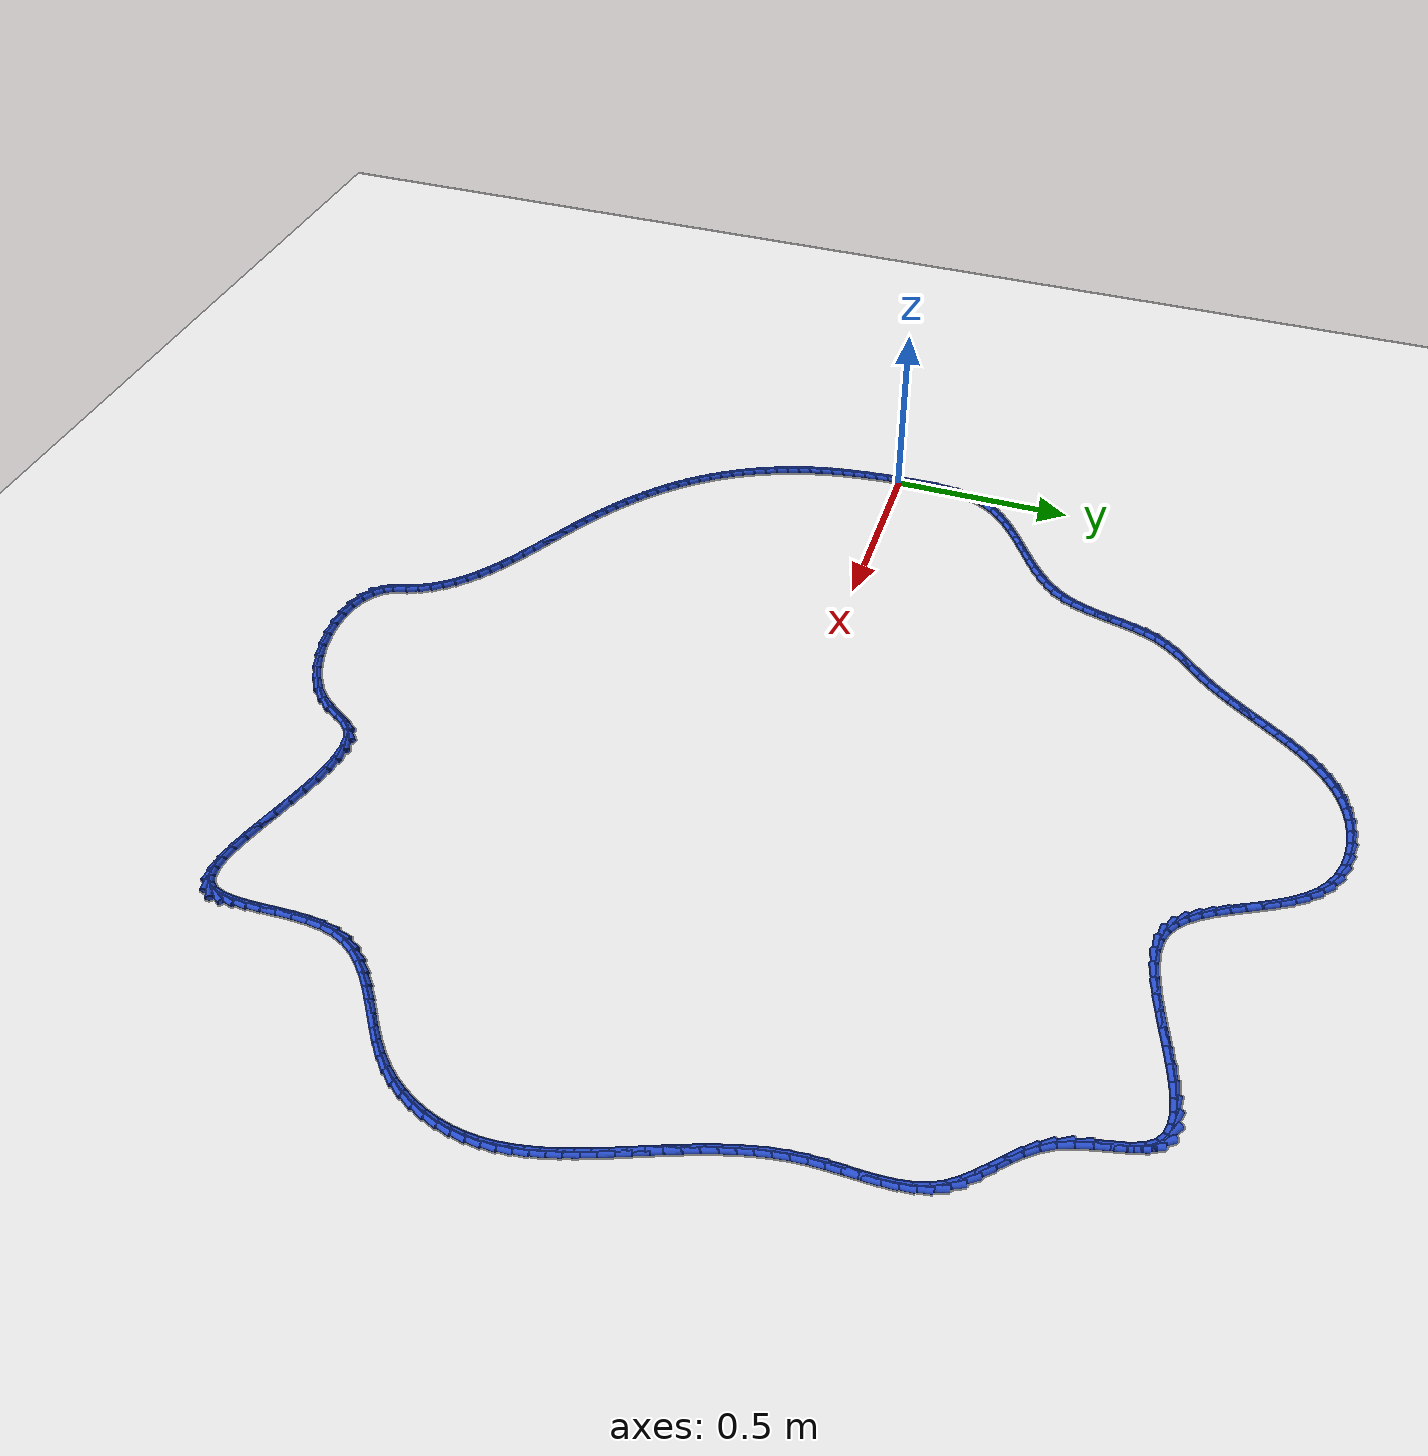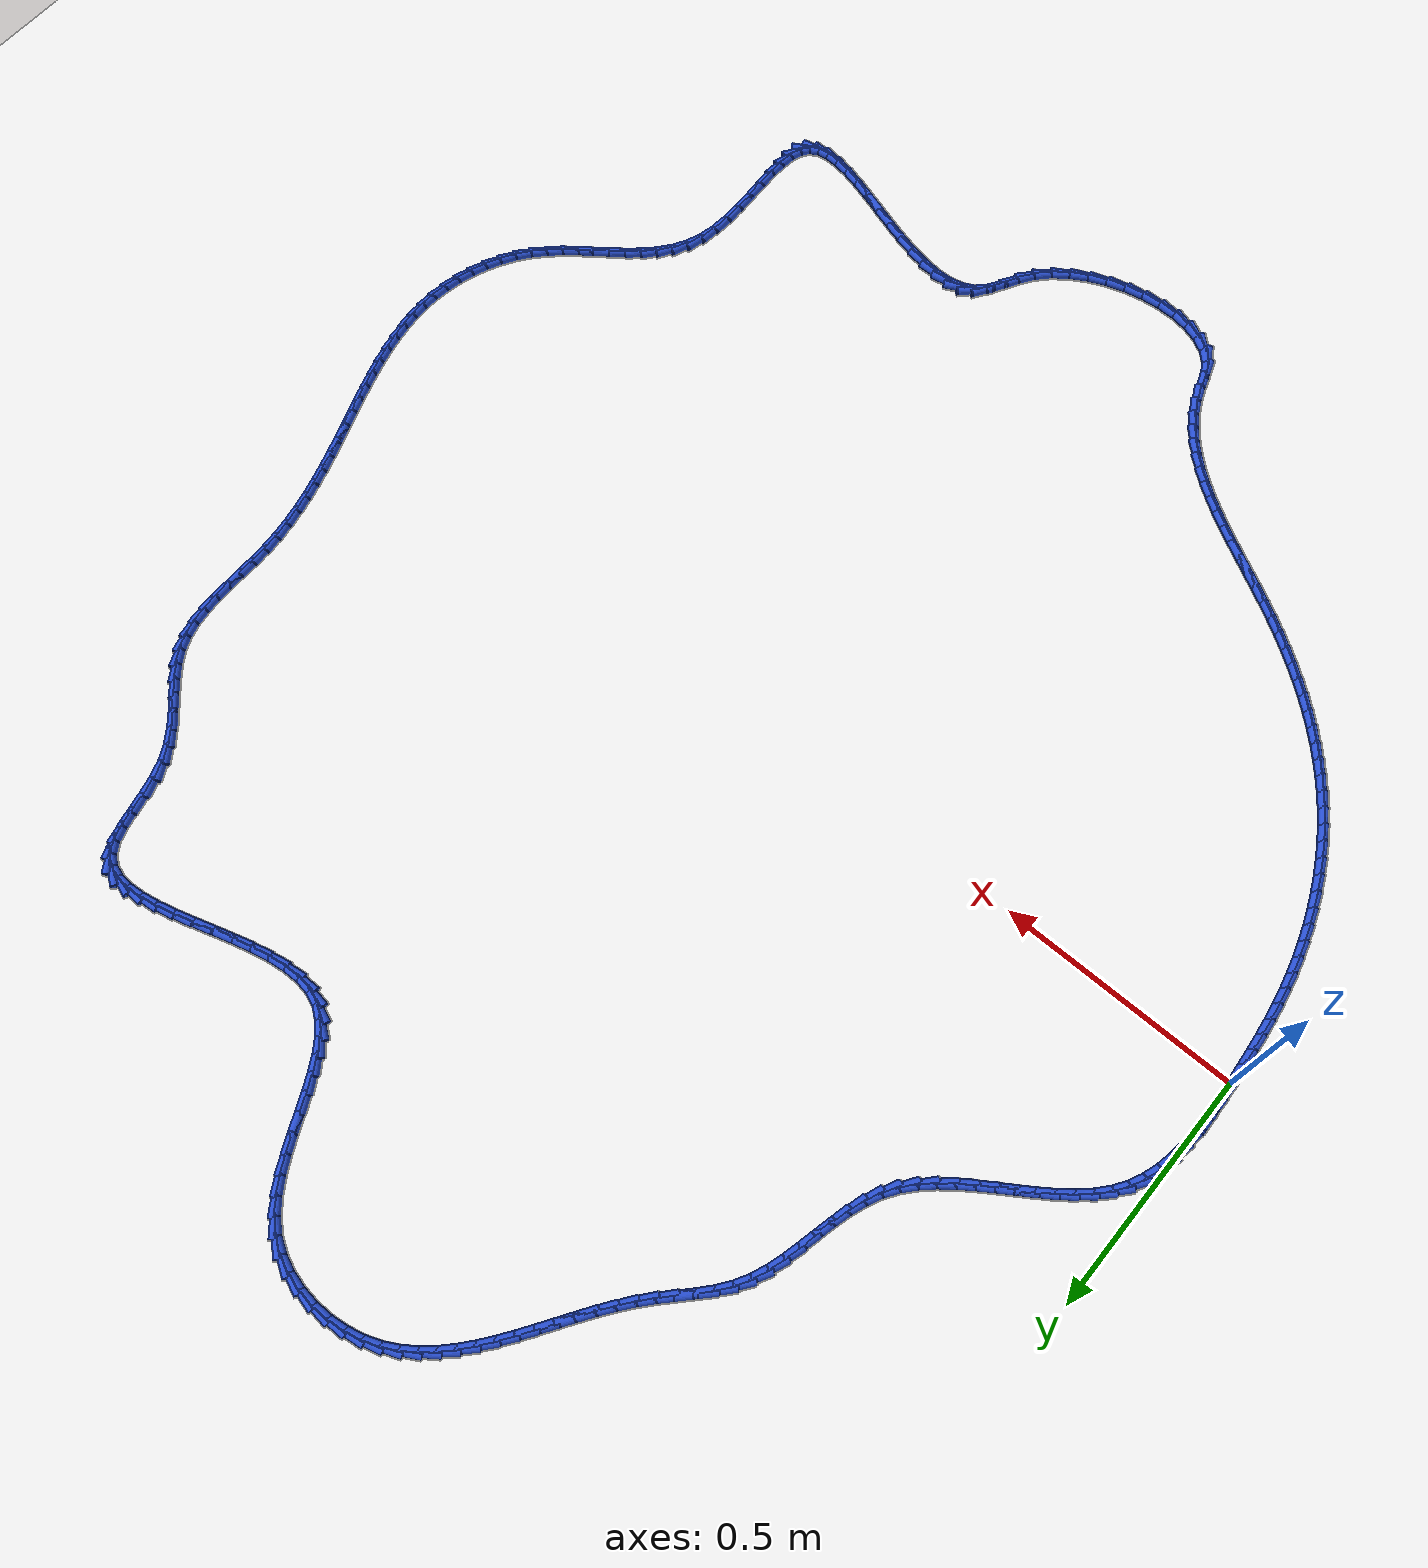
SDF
<sdf version="1.6">
 <world name="default">
  <light name="sun" type="directional">
   <pose>0 0 10 0 -0 0</pose>
   <diffuse>0.8 0.8 0.8 1</diffuse>
   <specular>0.2 0.2 0.2 1</specular>
   <attenuation>
    <range>1000</range>
    <constant>0.9</constant>
    <linear>0.01</linear>
    <quadratic>0.001</quadratic>
   </attenuation>
   <direction>-0.5 0.1 -0.9</direction>
  </light>
  <model name="ground_plane">
   <static>1</static>
   <link name="link">
    <collision name="collision">
     <geometry><plane><normal>0 0 1</normal><size>100 100</size></plane></geometry>
     <surface><friction><ode><mu>100</mu><mu2>50</mu2></ode></friction></surface>
    </collision>
    <visual name="visual">
     <cast_shadows>0</cast_shadows>
     <geometry><plane><normal>0 0 1</normal><size>100 100</size></plane></geometry>
     <material>
      <script><uri>file://media/materials/scripts/gazebo.material</uri><name>Gazebo/WhiteGlow</name></script>
     </material>
    </visual>
   </link>
  </model>
  <gravity>0 0 -9.8</gravity>
  <magnetic_field>6e-06 2.3e-05 -4.2e-05</magnetic_field>
  <atmosphere type="adiabatic"/>
  <physics name="default_physics" default="0" type="ode">
   <max_step_size>0.001</max_step_size>
   <real_time_factor>1</real_time_factor>
   <real_time_update_rate>1000</real_time_update_rate>
  </physics>
  <scene><ambient>0.4 0.4 0.4 1</ambient><background>0.7 0.7 0.7 1</background><shadows>1</shadows></scene>
  <spherical_coordinates>
   <surface_model>EARTH_WGS84</surface_model>
   <latitude_deg>0</latitude_deg>
   <longitude_deg>0</longitude_deg>
   <elevation>0</elevation>
   <heading_deg>0</heading_deg>
  </spherical_coordinates>
  <model name="line">
   <link name="link_0">
    <pose>-1.8865117801247777e-17 -6.938893903907228e-18 0.01 0 1.57 -1.5235107660359657</pose>
    <collision name="collision">
     <geometry><cylinder><radius>0.01</radius><length>0.08</length></cylinder></geometry>
    </collision>
    <visual name="visual">
     <material>
      <script><name>Gazebo/Blue</name><uri>file://media/materials/scripts/gazebo.material</uri></script>
     </material>
     <geometry><cylinder><radius>0.01</radius><length>0.08</length></cylinder></geometry>
    </visual>
   </link>
   <link name="link_1">
    <pose>-0.0016768079151093715 0.03543487617344846 0.01 0 1.57 -1.5468639049425708</pose>
    <collision name="collision">
     <geometry><cylinder><radius>0.01</radius><length>0.08</length></cylinder></geometry>
    </collision>
    <visual name="visual">
     <material>
      <script><name>Gazebo/Blue</name><uri>file://media/materials/scripts/gazebo.material</uri></script>
     </material>
     <geometry><cylinder><radius>0.01</radius><length>0.08</length></cylinder></geometry>
    </visual>
   </link>
   <link name="link_2">
    <pose>-0.002530282724119755 0.07108993283302313 0.01 0 1.57 1.5583452302952334</pose>
    <collision name="collision">
     <geometry><cylinder><radius>0.01</radius><length>0.08</length></cylinder></geometry>
    </collision>
    <visual name="visual">
     <material>
      <script><name>Gazebo/Blue</name><uri>file://media/materials/scripts/gazebo.material</uri></script>
     </material>
     <geometry><cylinder><radius>0.01</radius><length>0.08</length></cylinder></geometry>
    </visual>
   </link>
   <link name="link_3">
    <pose>-0.002088371365965157 0.10657986108580306 0.01 0 1.57 1.5076467822202162</pose>
    <collision name="collision">
     <geometry><cylinder><radius>0.01</radius><length>0.08</length></cylinder></geometry>
    </collision>
    <visual name="visual">
     <material>
      <script><name>Gazebo/Blue</name><uri>file://media/materials/scripts/gazebo.material</uri></script>
     </material>
     <geometry><cylinder><radius>0.01</radius><length>0.08</length></cylinder></geometry>
    </visual>
   </link>
   <link name="link_4">
    <pose>0.0001209792204204408 0.1415193520388671 0.01 0 1.57 1.4407013593807974</pose>
    <collision name="collision">
     <geometry><cylinder><radius>0.01</radius><length>0.08</length></cylinder></geometry>
    </collision>
    <visual name="visual">
     <material>
      <script><name>Gazebo/Blue</name><uri>file://media/materials/scripts/gazebo.material</uri></script>
     </material>
     <geometry><cylinder><radius>0.01</radius><length>0.08</length></cylinder></geometry>
    </visual>
   </link>
   <link name="link_5">
    <pose>0.004569822096103057 0.1755230967992941 0.01 0 1.57 1.3551159942801971</pose>
    <collision name="collision">
     <geometry><cylinder><radius>0.01</radius><length>0.08</length></cylinder></geometry>
    </collision>
    <visual name="visual">
     <material>
      <script><name>Gazebo/Blue</name><uri>file://media/materials/scripts/gazebo.material</uri></script>
     </material>
     <geometry><cylinder><radius>0.01</radius><length>0.08</length></cylinder></geometry>
    </visual>
   </link>
   <link name="link_6">
    <pose>0.01173021032214871 0.2082057864741631 0.01 0 1.57 1.24850706208488</pose>
    <collision name="collision">
     <geometry><cylinder><radius>0.01</radius><length>0.08</length></cylinder></geometry>
    </collision>
    <visual name="visual">
     <material>
      <script><name>Gazebo/Blue</name><uri>file://media/materials/scripts/gazebo.material</uri></script>
     </material>
     <geometry><cylinder><radius>0.01</radius><length>0.08</length></cylinder></geometry>
    </visual>
   </link>
   <link name="link_7">
    <pose>0.022074196959623413 0.23918211217055307 0.01 0 1.57 1.119484578515157</pose>
    <collision name="collision">
     <geometry><cylinder><radius>0.01</radius><length>0.08</length></cylinder></geometry>
    </collision>
    <visual name="visual">
     <material>
      <script><name>Gazebo/Blue</name><uri>file://media/materials/scripts/gazebo.material</uri></script>
     </material>
     <geometry><cylinder><radius>0.01</radius><length>0.08</length></cylinder></geometry>
    </visual>
   </link>
   <link name="link_8">
    <pose>0.03607383506959317 0.2680667649955427 0.01 0 1.57 0.9750801985812856</pose>
    <collision name="collision">
     <geometry><cylinder><radius>0.01</radius><length>0.08</length></cylinder></geometry>
    </collision>
    <visual name="visual">
     <material>
      <script><name>Gazebo/Blue</name><uri>file://media/materials/scripts/gazebo.material</uri></script>
     </material>
     <geometry><cylinder><radius>0.01</radius><length>0.08</length></cylinder></geometry>
    </visual>
   </link>
   <link name="link_9">
    <pose>0.054047725164523844 0.2945821585456801 0.01 0 1.57 0.8476703503692483</pose>
    <collision name="collision">
     <geometry><cylinder><radius>0.01</radius><length>0.08</length></cylinder></geometry>
    </collision>
    <visual name="visual">
     <material>
      <script><name>Gazebo/Blue</name><uri>file://media/materials/scripts/gazebo.material</uri></script>
     </material>
     <geometry><cylinder><radius>0.01</radius><length>0.08</length></cylinder></geometry>
    </visual>
   </link>
   <link name="link_10">
    <pose>0.07557351755015448 0.3189708476700976 0.01 0 1.57 0.7478165467816401</pose>
    <collision name="collision">
     <geometry><cylinder><radius>0.01</radius><length>0.08</length></cylinder></geometry>
    </collision>
    <visual name="visual">
     <material>
      <script><name>Gazebo/Blue</name><uri>file://media/materials/scripts/gazebo.material</uri></script>
     </material>
     <geometry><cylinder><radius>0.01</radius><length>0.08</length></cylinder></geometry>
    </visual>
   </link>
   <link name="link_11">
    <pose>0.10000551932537141 0.34163217240310434 0.01 0 1.57 0.674269142136977</pose>
    <collision name="collision">
     <geometry><cylinder><radius>0.01</radius><length>0.08</length></cylinder></geometry>
    </collision>
    <visual name="visual">
     <material>
      <script><name>Gazebo/Blue</name><uri>file://media/materials/scripts/gazebo.material</uri></script>
     </material>
     <geometry><cylinder><radius>0.01</radius><length>0.08</length></cylinder></geometry>
    </visual>
   </link>
   <link name="link_12">
    <pose>0.12669799187099895 0.36296550487273166 0.01 0 1.57 0.6245701626853636</pose>
    <collision name="collision">
     <geometry><cylinder><radius>0.01</radius><length>0.08</length></cylinder></geometry>
    </collision>
    <visual name="visual">
     <material>
      <script><name>Gazebo/Blue</name><uri>file://media/materials/scripts/gazebo.material</uri></script>
     </material>
     <geometry><cylinder><radius>0.01</radius><length>0.08</length></cylinder></geometry>
    </visual>
   </link>
   <link name="link_13">
    <pose>0.15500519656786144 0.38337021720701103 0.01 0 1.57 0.5964206562703848</pose>
    <collision name="collision">
     <geometry><cylinder><radius>0.01</radius><length>0.08</length></cylinder></geometry>
    </collision>
    <visual name="visual">
     <material>
      <script><name>Gazebo/Blue</name><uri>file://media/materials/scripts/gazebo.material</uri></script>
     </material>
     <geometry><cylinder><radius>0.01</radius><length>0.08</length></cylinder></geometry>
    </visual>
   </link>
   <link name="link_14">
    <pose>0.18428139479678346 0.4032456815339739 0.01 0 1.57 0.5882977099093772</pose>
    <collision name="collision">
     <geometry><cylinder><radius>0.01</radius><length>0.08</length></cylinder></geometry>
    </collision>
    <visual name="visual">
     <material>
      <script><name>Gazebo/Blue</name><uri>file://media/materials/scripts/gazebo.material</uri></script>
     </material>
     <geometry><cylinder><radius>0.01</radius><length>0.08</length></cylinder></geometry>
    </visual>
   </link>
   <link name="link_15">
    <pose>0.21388084793858925 0.4229912699816514 0.01 0 1.57 0.5996656336511133</pose>
    <collision name="collision">
     <geometry><cylinder><radius>0.01</radius><length>0.08</length></cylinder></geometry>
    </collision>
    <visual name="visual">
     <material>
      <script><name>Gazebo/Blue</name><uri>file://media/materials/scripts/gazebo.material</uri></script>
     </material>
     <geometry><cylinder><radius>0.01</radius><length>0.08</length></cylinder></geometry>
    </visual>
   </link>
   <link name="link_16">
    <pose>0.24315781737410327 0.44300635467807487 0.01 0 1.57 0.6310055048117249</pose>
    <collision name="collision">
     <geometry><cylinder><radius>0.01</radius><length>0.08</length></cylinder></geometry>
    </collision>
    <visual name="visual">
     <material>
      <script><name>Gazebo/Blue</name><uri>file://media/materials/scripts/gazebo.material</uri></script>
     </material>
     <geometry><cylinder><radius>0.01</radius><length>0.08</length></cylinder></geometry>
    </visual>
   </link>
   <link name="link_17">
    <pose>0.27146656448414996 0.46369030775127584 0.01 0 1.57 0.6837292656225489</pose>
    <collision name="collision">
     <geometry><cylinder><radius>0.01</radius><length>0.08</length></cylinder></geometry>
    </collision>
    <visual name="visual">
     <material>
      <script><name>Gazebo/Blue</name><uri>file://media/materials/scripts/gazebo.material</uri></script>
     </material>
     <geometry><cylinder><radius>0.01</radius><length>0.08</length></cylinder></geometry>
    </visual>
   </link>
   <link name="link_18">
    <pose>0.2981613506495537 0.4854425013292857 0.01 0 1.57 0.7599019976356562</pose>
    <collision name="collision">
     <geometry><cylinder><radius>0.01</radius><length>0.08</length></cylinder></geometry>
    </collision>
    <visual name="visual">
     <material>
      <script><name>Gazebo/Blue</name><uri>file://media/materials/scripts/gazebo.material</uri></script>
     </material>
     <geometry><cylinder><radius>0.01</radius><length>0.08</length></cylinder></geometry>
    </visual>
   </link>
   <link name="link_19">
    <pose>0.32259643725113873 0.5086623075401355 0.01 0 1.57 0.8615571871883946</pose>
    <collision name="collision">
     <geometry><cylinder><radius>0.01</radius><length>0.08</length></cylinder></geometry>
    </collision>
    <visual name="visual">
     <material>
      <script><name>Gazebo/Blue</name><uri>file://media/materials/scripts/gazebo.material</uri></script>
     </material>
     <geometry><cylinder><radius>0.01</radius><length>0.08</length></cylinder></geometry>
    </visual>
   </link>
   <link name="link_20">
    <pose>0.34412608566972963 0.5337490985118567 0.01 0 1.57 0.9892517016680953</pose>
    <collision name="collision">
     <geometry><cylinder><radius>0.01</radius><length>0.08</length></cylinder></geometry>
    </collision>
    <visual name="visual">
     <material>
      <script><name>Gazebo/Blue</name><uri>file://media/materials/scripts/gazebo.material</uri></script>
     </material>
     <geometry><cylinder><radius>0.01</radius><length>0.08</length></cylinder></geometry>
    </visual>
   </link>
   <link name="link_21">
    <pose>0.3621066092203056 0.5611009636002877 0.01 0 1.57 1.1245489932387878</pose>
    <collision name="collision">
     <geometry><cylinder><radius>0.01</radius><length>0.08</length></cylinder></geometry>
    </collision>
    <visual name="visual">
     <material>
      <script><name>Gazebo/Blue</name><uri>file://media/materials/scripts/gazebo.material</uri></script>
     </material>
     <geometry><cylinder><radius>0.01</radius><length>0.08</length></cylinder></geometry>
    </visual>
   </link>
   <link name="link_22">
    <pose>0.3763350365631058 0.5908404777697857 0.01 0 1.57 1.2288416815091314</pose>
    <collision name="collision">
     <geometry><cylinder><radius>0.01</radius><length>0.08</length></cylinder></geometry>
    </collision>
    <visual name="visual">
     <material>
      <script><name>Gazebo/Blue</name><uri>file://media/materials/scripts/gazebo.material</uri></script>
     </material>
     <geometry><cylinder><radius>0.01</radius><length>0.08</length></cylinder></geometry>
    </visual>
   </link>
   <link name="link_23">
    <pose>0.387594507197375 0.6224737461234643 0.01 0 1.57 1.2983034303193903</pose>
    <collision name="collision">
     <geometry><cylinder><radius>0.01</radius><length>0.08</length></cylinder></geometry>
    </collision>
    <visual name="visual">
     <material>
      <script><name>Gazebo/Blue</name><uri>file://media/materials/scripts/gazebo.material</uri></script>
     </material>
     <geometry><cylinder><radius>0.01</radius><length>0.08</length></cylinder></geometry>
    </visual>
   </link>
   <link name="link_24">
    <pose>0.3968020255121778 0.6554231877660794 0.01 0 1.57 1.3356038408064639</pose>
    <collision name="collision">
     <geometry><cylinder><radius>0.01</radius><length>0.08</length></cylinder></geometry>
    </collision>
    <visual name="visual">
     <material>
      <script><name>Gazebo/Blue</name><uri>file://media/materials/scripts/gazebo.material</uri></script>
     </material>
     <geometry><cylinder><radius>0.01</radius><length>0.08</length></cylinder></geometry>
    </visual>
   </link>
   <link name="link_25">
    <pose>0.40487459589657865 0.6891112218023867 0.01 0 1.57 1.342783047570714</pose>
    <collision name="collision">
     <geometry><cylinder><radius>0.01</radius><length>0.08</length></cylinder></geometry>
    </collision>
    <visual name="visual">
     <material>
      <script><name>Gazebo/Blue</name><uri>file://media/materials/scripts/gazebo.material</uri></script>
     </material>
     <geometry><cylinder><radius>0.01</radius><length>0.08</length></cylinder></geometry>
    </visual>
   </link>
   <link name="link_26">
    <pose>0.41272922273964247 0.7229602673371428 0.01 0 1.57 1.3203197230353265</pose>
    <collision name="collision">
     <geometry><cylinder><radius>0.01</radius><length>0.08</length></cylinder></geometry>
    </collision>
    <visual name="visual">
     <material>
      <script><name>Gazebo/Blue</name><uri>file://media/materials/scripts/gazebo.material</uri></script>
     </material>
     <geometry><cylinder><radius>0.01</radius><length>0.08</length></cylinder></geometry>
    </visual>
   </link>
   <link name="link_27">
    <pose>0.4212829104304337 0.7563927434751038 0.01 0 1.57 1.266991204948427</pose>
    <collision name="collision">
     <geometry><cylinder><radius>0.01</radius><length>0.08</length></cylinder></geometry>
    </collision>
    <visual name="visual">
     <material>
      <script><name>Gazebo/Blue</name><uri>file://media/materials/scripts/gazebo.material</uri></script>
     </material>
     <geometry><cylinder><radius>0.01</radius><length>0.08</length></cylinder></geometry>
    </visual>
   </link>
   <link name="link_28">
    <pose>0.431452663358017 0.7888310693210253 0.01 0 1.57 1.1803818665584005</pose>
    <collision name="collision">
     <geometry><cylinder><radius>0.01</radius><length>0.08</length></cylinder></geometry>
    </collision>
    <visual name="visual">
     <material>
      <script><name>Gazebo/Blue</name><uri>file://media/materials/scripts/gazebo.material</uri></script>
     </material>
     <geometry><cylinder><radius>0.01</radius><length>0.08</length></cylinder></geometry>
    </visual>
   </link>
   <link name="link_29">
    <pose>0.44415548591145704 0.8196976639796636 0.01 0 1.57 1.059244512512648</pose>
    <collision name="collision">
     <geometry><cylinder><radius>0.01</radius><length>0.08</length></cylinder></geometry>
    </collision>
    <visual name="visual">
     <material>
      <script><name>Gazebo/Blue</name><uri>file://media/materials/scripts/gazebo.material</uri></script>
     </material>
     <geometry><cylinder><radius>0.01</radius><length>0.08</length></cylinder></geometry>
    </visual>
   </link>
   <link name="link_30">
    <pose>0.46028606394032745 0.8484305463985041 0.01 0 1.57 0.9360042531074427</pose>
    <collision name="collision">
     <geometry><cylinder><radius>0.01</radius><length>0.08</length></cylinder></geometry>
    </collision>
    <visual name="visual">
     <material>
      <script><name>Gazebo/Blue</name><uri>file://media/materials/scripts/gazebo.material</uri></script>
     </material>
     <geometry><cylinder><radius>0.01</radius><length>0.08</length></cylinder></geometry>
    </visual>
   </link>
   <link name="link_31">
    <pose>0.4798959549823933 0.875057051374757 0.01 0 1.57 0.8537790698344769</pose>
    <collision name="collision">
     <geometry><cylinder><radius>0.01</radius><length>0.08</length></cylinder></geometry>
    </collision>
    <visual name="visual">
     <material>
      <script><name>Gazebo/Blue</name><uri>file://media/materials/scripts/gazebo.material</uri></script>
     </material>
     <geometry><cylinder><radius>0.01</radius><length>0.08</length></cylinder></geometry>
    </visual>
   </link>
   <link name="link_32">
    <pose>0.5019554323750671 0.900360291810105 0.01 0 1.57 0.8145092933418777</pose>
    <collision name="collision">
     <geometry><cylinder><radius>0.01</radius><length>0.08</length></cylinder></geometry>
    </collision>
    <visual name="visual">
     <material>
      <script><name>Gazebo/Blue</name><uri>file://media/materials/scripts/gazebo.material</uri></script>
     </material>
     <geometry><cylinder><radius>0.01</radius><length>0.08</length></cylinder></geometry>
    </visual>
   </link>
   <link name="link_33">
    <pose>0.5253638936673601 0.925172920189804 0.01 0 1.57 0.8160744558498942</pose>
    <collision name="collision">
     <geometry><cylinder><radius>0.01</radius><length>0.08</length></cylinder></geometry>
    </collision>
    <visual name="visual">
     <material>
      <script><name>Gazebo/Blue</name><uri>file://media/materials/scripts/gazebo.material</uri></script>
     </material>
     <geometry><cylinder><radius>0.01</radius><length>0.08</length></cylinder></geometry>
    </visual>
   </link>
   <link name="link_34">
    <pose>0.5490207364082835 0.9503275889991104 0.01 0 1.57 0.8560017176470157</pose>
    <collision name="collision">
     <geometry><cylinder><radius>0.01</radius><length>0.08</length></cylinder></geometry>
    </collision>
    <visual name="visual">
     <material>
      <script><name>Gazebo/Blue</name><uri>file://media/materials/scripts/gazebo.material</uri></script>
     </material>
     <geometry><cylinder><radius>0.01</radius><length>0.08</length></cylinder></geometry>
    </visual>
   </link>
   <link name="link_35">
    <pose>0.5718519819214575 0.9766338965611188 0.01 0 1.57 0.9088975280710291</pose>
    <collision name="collision">
     <geometry><cylinder><radius>0.01</radius><length>0.08</length></cylinder></geometry>
    </collision>
    <visual name="visual">
     <material>
      <script><name>Gazebo/Blue</name><uri>file://media/materials/scripts/gazebo.material</uri></script>
     </material>
     <geometry><cylinder><radius>0.01</radius><length>0.08</length></cylinder></geometry>
    </visual>
   </link>
   <link name="link_36">
    <pose>0.5934363363102734 1.0043362658631592 0.01 0 1.57 0.9493742972569054</pose>
    <collision name="collision">
     <geometry><cylinder><radius>0.01</radius><length>0.08</length></cylinder></geometry>
    </collision>
    <visual name="visual">
     <material>
      <script><name>Gazebo/Blue</name><uri>file://media/materials/scripts/gazebo.material</uri></script>
     </material>
     <geometry><cylinder><radius>0.01</radius><length>0.08</length></cylinder></geometry>
    </visual>
   </link>
   <link name="link_37">
    <pose>0.6140284195388198 1.0330938299409567 0.01 0 1.57 0.9768027827212767</pose>
    <collision name="collision">
     <geometry><cylinder><radius>0.01</radius><length>0.08</length></cylinder></geometry>
    </collision>
    <visual name="visual">
     <material>
      <script><name>Gazebo/Blue</name><uri>file://media/materials/scripts/gazebo.material</uri></script>
     </material>
     <geometry><cylinder><radius>0.01</radius><length>0.08</length></cylinder></geometry>
    </visual>
   </link>
   <link name="link_38">
    <pose>0.6339141229431926 1.062538643202508 0.01 0 1.57 0.9916264712208274</pose>
    <collision name="collision">
     <geometry><cylinder><radius>0.01</radius><length>0.08</length></cylinder></geometry>
    </collision>
    <visual name="visual">
     <material>
      <script><name>Gazebo/Blue</name><uri>file://media/materials/scripts/gazebo.material</uri></script>
     </material>
     <geometry><cylinder><radius>0.01</radius><length>0.08</length></cylinder></geometry>
    </visual>
   </link>
   <link name="link_39">
    <pose>0.653379337859489 1.092302760055811 0.01 0 1.57 0.9940531078447946</pose>
    <collision name="collision">
     <geometry><cylinder><radius>0.01</radius><length>0.08</length></cylinder></geometry>
    </collision>
    <visual name="visual">
     <material>
      <script><name>Gazebo/Blue</name><uri>file://media/materials/scripts/gazebo.material</uri></script>
     </material>
     <geometry><cylinder><radius>0.01</radius><length>0.08</length></cylinder></geometry>
    </visual>
   </link>
   <link name="link_40">
    <pose>0.672709955623805 1.1220182349088634 0.01 0 1.57 0.9839921941714765</pose>
    <collision name="collision">
     <geometry><cylinder><radius>0.01</radius><length>0.08</length></cylinder></geometry>
    </collision>
    <visual name="visual">
     <material>
      <script><name>Gazebo/Blue</name><uri>file://media/materials/scripts/gazebo.material</uri></script>
     </material>
     <geometry><cylinder><radius>0.01</radius><length>0.08</length></cylinder></geometry>
    </visual>
   </link>
   <link name="link_41">
    <pose>0.6921918675722372 1.151317122169663 0.01 0 1.57 0.9610348600286166</pose>
    <collision name="collision">
     <geometry><cylinder><radius>0.01</radius><length>0.08</length></cylinder></geometry>
    </collision>
    <visual name="visual">
     <material>
      <script><name>Gazebo/Blue</name><uri>file://media/materials/scripts/gazebo.material</uri></script>
     </material>
     <geometry><cylinder><radius>0.01</radius><length>0.08</length></cylinder></geometry>
    </visual>
   </link>
   <link name="link_42">
    <pose>0.7121109650408821 1.179831476246207 0.01 0 1.57 0.9244764120487332</pose>
    <collision name="collision">
     <geometry><cylinder><radius>0.01</radius><length>0.08</length></cylinder></geometry>
    </collision>
    <visual name="visual">
     <material>
      <script><name>Gazebo/Blue</name><uri>file://media/materials/scripts/gazebo.material</uri></script>
     </material>
     <geometry><cylinder><radius>0.01</radius><length>0.08</length></cylinder></geometry>
    </visual>
   </link>
   <link name="link_43">
    <pose>0.7327531393658359 1.2071933515464925 0.01 0 1.57 0.8734010545532254</pose>
    <collision name="collision">
     <geometry><cylinder><radius>0.01</radius><length>0.08</length></cylinder></geometry>
    </collision>
    <visual name="visual">
     <material>
      <script><name>Gazebo/Blue</name><uri>file://media/materials/scripts/gazebo.material</uri></script>
     </material>
     <geometry><cylinder><radius>0.01</radius><length>0.08</length></cylinder></geometry>
    </visual>
   </link>
   <link name="link_44">
    <pose>0.7544042818831956 1.233034802478518 0.01 0 1.57 0.8068681818872365</pose>
    <collision name="collision">
     <geometry><cylinder><radius>0.01</radius><length>0.08</length></cylinder></geometry>
    </collision>
    <visual name="visual">
     <material>
      <script><name>Gazebo/Blue</name><uri>file://media/materials/scripts/gazebo.material</uri></script>
     </material>
     <geometry><cylinder><radius>0.01</radius><length>0.08</length></cylinder></geometry>
    </visual>
   </link>
   <link name="link_45">
    <pose>0.7773502839290571 1.2569878834502801 0.01 0 1.57 0.7242505144768826</pose>
    <collision name="collision">
     <geometry><cylinder><radius>0.01</radius><length>0.08</length></cylinder></geometry>
    </collision>
    <visual name="visual">
     <material>
      <script><name>Gazebo/Blue</name><uri>file://media/materials/scripts/gazebo.material</uri></script>
     </material>
     <geometry><cylinder><radius>0.01</radius><length>0.08</length></cylinder></geometry>
    </visual>
   </link>
   <link name="link_46">
    <pose>0.8018770368395173 1.278684648869777 0.01 0 1.57 0.6257491263448781</pose>
    <collision name="collision">
     <geometry><cylinder><radius>0.01</radius><length>0.08</length></cylinder></geometry>
    </collision>
    <visual name="visual">
     <material>
      <script><name>Gazebo/Blue</name><uri>file://media/materials/scripts/gazebo.material</uri></script>
     </material>
     <geometry><cylinder><radius>0.01</radius><length>0.08</length></cylinder></geometry>
    </visual>
   </link>
   <link name="link_47">
    <pose>0.8282704319506725 1.2977571531450058 0.01 0 1.57 0.5130069648264336</pose>
    <collision name="collision">
     <geometry><cylinder><radius>0.01</radius><length>0.08</length></cylinder></geometry>
    </collision>
    <visual name="visual">
     <material>
      <script><name>Gazebo/Blue</name><uri>file://media/materials/scripts/gazebo.material</uri></script>
     </material>
     <geometry><cylinder><radius>0.01</radius><length>0.08</length></cylinder></geometry>
    </visual>
   </link>
   <link name="link_48">
    <pose>0.856816360598619 1.3138374506839645 0.01 0 1.57 0.38958705937239546</pose>
    <collision name="collision">
     <geometry><cylinder><radius>0.01</radius><length>0.08</length></cylinder></geometry>
    </collision>
    <visual name="visual">
     <material>
      <script><name>Gazebo/Blue</name><uri>file://media/materials/scripts/gazebo.material</uri></script>
     </material>
     <geometry><cylinder><radius>0.01</radius><length>0.08</length></cylinder></geometry>
    </visual>
   </link>
   <link name="link_49">
    <pose>0.8877986054079618 1.3265579016812616 0.01 0 1.57 0.26474297526489365</pose>
    <collision name="collision">
     <geometry><cylinder><radius>0.01</radius><length>0.08</length></cylinder></geometry>
    </collision>
    <visual name="visual">
     <material>
      <script><name>Gazebo/Blue</name><uri>file://media/materials/scripts/gazebo.material</uri></script>
     </material>
     <geometry><cylinder><radius>0.01</radius><length>0.08</length></cylinder></geometry>
    </visual>
   </link>
   <link name="link_50">
    <pose>0.921154980119249 1.3356010356663819 0.01 0 1.57 0.14644475062112777</pose>
    <collision name="collision">
     <geometry><cylinder><radius>0.01</radius><length>0.08</length></cylinder></geometry>
    </collision>
    <visual name="visual">
     <material>
      <script><name>Gazebo/Blue</name><uri>file://media/materials/scripts/gazebo.material</uri></script>
     </material>
     <geometry><cylinder><radius>0.01</radius><length>0.08</length></cylinder></geometry>
    </visual>
   </link>
   <link name="link_51">
    <pose>0.9560959591592424 1.3407548544562895 0.01 0 1.57 0.02989289702175234</pose>
    <collision name="collision">
     <geometry><cylinder><radius>0.01</radius><length>0.08</length></cylinder></geometry>
    </collision>
    <visual name="visual">
     <material>
      <script><name>Gazebo/Blue</name><uri>file://media/materials/scripts/gazebo.material</uri></script>
     </material>
     <geometry><cylinder><radius>0.01</radius><length>0.08</length></cylinder></geometry>
    </visual>
   </link>
   <link name="link_52">
    <pose>0.9917401587339818 1.3418206803312893 0.01 0 1.57 -0.09056647365757871</pose>
    <collision name="collision">
     <geometry><cylinder><radius>0.01</radius><length>0.08</length></cylinder></geometry>
    </collision>
    <visual name="visual">
     <material>
      <script><name>Gazebo/Blue</name><uri>file://media/materials/scripts/gazebo.material</uri></script>
     </material>
     <geometry><cylinder><radius>0.01</radius><length>0.08</length></cylinder></geometry>
    </visual>
   </link>
   <link name="link_53">
    <pose>1.0272061950495066 1.3385998355716857 0.01 0 1.57 -0.22033860987775225</pose>
    <collision name="collision">
     <geometry><cylinder><radius>0.01</radius><length>0.08</length></cylinder></geometry>
    </collision>
    <visual name="visual">
     <material>
      <script><name>Gazebo/Blue</name><uri>file://media/materials/scripts/gazebo.material</uri></script>
     </material>
     <geometry><cylinder><radius>0.01</radius><length>0.08</length></cylinder></geometry>
    </visual>
   </link>
   <link name="link_54">
    <pose>1.0616126843118558 1.3308936424577824 0.01 0 1.57 -0.364581000922915</pose>
    <collision name="collision">
     <geometry><cylinder><radius>0.01</radius><length>0.08</length></cylinder></geometry>
    </collision>
    <visual name="visual">
     <material>
      <script><name>Gazebo/Blue</name><uri>file://media/materials/scripts/gazebo.material</uri></script>
     </material>
     <geometry><cylinder><radius>0.01</radius><length>0.08</length></cylinder></geometry>
    </visual>
   </link>
   <link name="link_55">
    <pose>1.0940782427270697 1.3185034232698842 0.01 0 1.57 -0.5275968643137261</pose>
    <collision name="collision">
     <geometry><cylinder><radius>0.01</radius><length>0.08</length></cylinder></geometry>
    </collision>
    <visual name="visual">
     <material>
      <script><name>Gazebo/Blue</name><uri>file://media/materials/scripts/gazebo.material</uri></script>
     </material>
     <geometry><cylinder><radius>0.01</radius><length>0.08</length></cylinder></geometry>
    </visual>
   </link>
   <link name="link_56">
    <pose>1.1237214865011869 1.3012305002882951 0.01 0 1.57 -0.7033818405725583</pose>
    <collision name="collision">
     <geometry><cylinder><radius>0.01</radius><length>0.08</length></cylinder></geometry>
    </collision>
    <visual name="visual">
     <material>
      <script><name>Gazebo/Blue</name><uri>file://media/materials/scripts/gazebo.material</uri></script>
     </material>
     <geometry><cylinder><radius>0.01</radius><length>0.08</length></cylinder></geometry>
    </visual>
   </link>
   <link name="link_57">
    <pose>1.1498809053007506 1.2790450633469599 0.01 0 1.57 -0.8536291593091401</pose>
    <collision name="collision">
     <geometry><cylinder><radius>0.01</radius><length>0.08</length></cylinder></geometry>
    </collision>
    <visual name="visual">
     <material>
      <script><name>Gazebo/Blue</name><uri>file://media/materials/scripts/gazebo.material</uri></script>
     </material>
     <geometry><cylinder><radius>0.01</radius><length>0.08</length></cylinder></geometry>
    </visual>
   </link>
   <link name="link_58">
    <pose>1.1728790646575975 1.2526730937409132 0.01 0 1.57 -0.9669033544255915</pose>
    <collision name="collision">
     <geometry><cylinder><radius>0.01</radius><length>0.08</length></cylinder></geometry>
    </collision>
    <visual name="visual">
     <material>
      <script><name>Gazebo/Blue</name><uri>file://media/materials/scripts/gazebo.material</uri></script>
     </material>
     <geometry><cylinder><radius>0.01</radius><length>0.08</length></cylinder></geometry>
    </visual>
   </link>
   <link name="link_59">
    <pose>1.193313730625599 1.2230519326938054 0.01 0 1.57 -1.0464363392796399</pose>
    <collision name="collision">
     <geometry><cylinder><radius>0.01</radius><length>0.08</length></cylinder></geometry>
    </collision>
    <visual name="visual">
     <material>
      <script><name>Gazebo/Blue</name><uri>file://media/materials/scripts/gazebo.material</uri></script>
     </material>
     <geometry><cylinder><radius>0.01</radius><length>0.08</length></cylinder></geometry>
    </visual>
   </link>
   <link name="link_60">
    <pose>1.2117826821778939 1.191118931351564 0.01 0 1.57 -1.096463690850568</pose>
    <collision name="collision">
     <geometry><cylinder><radius>0.01</radius><length>0.08</length></cylinder></geometry>
    </collision>
    <visual name="visual">
     <material>
      <script><name>Gazebo/Blue</name><uri>file://media/materials/scripts/gazebo.material</uri></script>
     </material>
     <geometry><cylinder><radius>0.01</radius><length>0.08</length></cylinder></geometry>
    </visual>
   </link>
   <link name="link_61">
    <pose>1.2288836982876246 1.1578114408601172 0.01 0 1.57 -1.1200674420037786</pose>
    <collision name="collision">
     <geometry><cylinder><radius>0.01</radius><length>0.08</length></cylinder></geometry>
    </collision>
    <visual name="visual">
     <material>
      <script><name>Gazebo/Blue</name><uri>file://media/materials/scripts/gazebo.material</uri></script>
     </material>
     <geometry><cylinder><radius>0.01</radius><length>0.08</length></cylinder></geometry>
    </visual>
   </link>
   <link name="link_62">
    <pose>1.2452145579279301 1.1240668123653925 0.01 0 1.57 -1.1183700401109224</pose>
    <collision name="collision">
     <geometry><cylinder><radius>0.01</radius><length>0.08</length></cylinder></geometry>
    </collision>
    <visual name="visual">
     <material>
      <script><name>Gazebo/Blue</name><uri>file://media/materials/scripts/gazebo.material</uri></script>
     </material>
     <geometry><cylinder><radius>0.01</radius><length>0.08</length></cylinder></geometry>
    </visual>
   </link>
   <link name="link_63">
    <pose>1.2613730400719512 1.0908223970133168 0.01 0 1.57 -1.0901808059059932</pose>
    <collision name="collision">
     <geometry><cylinder><radius>0.01</radius><length>0.08</length></cylinder></geometry>
    </collision>
    <visual name="visual">
     <material>
      <script><name>Gazebo/Blue</name><uri>file://media/materials/scripts/gazebo.material</uri></script>
     </material>
     <geometry><cylinder><radius>0.01</radius><length>0.08</length></cylinder></geometry>
    </visual>
   </link>
   <link name="link_64">
    <pose>1.277956923692828 1.059015545949819 0.01 0 1.57 -1.0316793830379891</pose>
    <collision name="collision">
     <geometry><cylinder><radius>0.01</radius><length>0.08</length></cylinder></geometry>
    </collision>
    <visual name="visual">
     <material>
      <script><name>Gazebo/Blue</name><uri>file://media/materials/scripts/gazebo.material</uri></script>
     </material>
     <geometry><cylinder><radius>0.01</radius><length>0.08</length></cylinder></geometry>
    </visual>
   </link>
   <link name="link_65">
    <pose>1.2955639877637013 1.0295836103208258 0.01 0 1.57 -0.9362175802798904</pose>
    <collision name="collision">
     <geometry><cylinder><radius>0.01</radius><length>0.08</length></cylinder></geometry>
    </collision>
    <visual name="visual">
     <material>
      <script><name>Gazebo/Blue</name><uri>file://media/materials/scripts/gazebo.material</uri></script>
     </material>
     <geometry><cylinder><radius>0.01</radius><length>0.08</length></cylinder></geometry>
    </visual>
   </link>
   <link name="link_66">
    <pose>1.3147920112577114 1.0034639412722648 0.01 0 1.57 -0.7951697954236493</pose>
    <collision name="collision">
     <geometry><cylinder><radius>0.01</radius><length>0.08</length></cylinder></geometry>
    </collision>
    <visual name="visual">
     <material>
      <script><name>Gazebo/Blue</name><uri>file://media/materials/scripts/gazebo.material</uri></script>
     </material>
     <geometry><cylinder><radius>0.01</radius><length>0.08</length></cylinder></geometry>
    </visual>
   </link>
   <link name="link_67">
    <pose>1.336238773147998 0.9815938899500644 0.01 0 1.57 -0.6023454986765686</pose>
    <collision name="collision">
     <geometry><cylinder><radius>0.01</radius><length>0.08</length></cylinder></geometry>
    </collision>
    <visual name="visual">
     <material>
      <script><name>Gazebo/Blue</name><uri>file://media/materials/scripts/gazebo.material</uri></script>
     </material>
     <geometry><cylinder><radius>0.01</radius><length>0.08</length></cylinder></geometry>
    </visual>
   </link>
   <link name="link_68">
    <pose>1.3605020524077027 0.9649108075001517 0.01 0 1.57 -0.36477550084368865</pose>
    <collision name="collision">
     <geometry><cylinder><radius>0.01</radius><length>0.08</length></cylinder></geometry>
    </collision>
    <visual name="visual">
     <material>
      <script><name>Gazebo/Blue</name><uri>file://media/materials/scripts/gazebo.material</uri></script>
     </material>
     <geometry><cylinder><radius>0.01</radius><length>0.08</length></cylinder></geometry>
    </visual>
   </link>
   <link name="link_69">
    <pose>1.3881743820241197 0.9543437188684959 0.01 0 1.57 -0.1336845446923936</pose>
    <collision name="collision">
     <geometry><cylinder><radius>0.01</radius><length>0.08</length></cylinder></geometry>
    </collision>
    <visual name="visual">
     <material>
      <script><name>Gazebo/Blue</name><uri>file://media/materials/scripts/gazebo.material</uri></script>
     </material>
     <geometry><cylinder><radius>0.01</radius><length>0.08</length></cylinder></geometry>
    </visual>
   </link>
   <link name="link_70">
    <pose>1.4194198385829515 0.9501416216852142 0.01 0 1.57 0.03615019294212959</pose>
    <collision name="collision">
     <geometry><cylinder><radius>0.01</radius><length>0.08</length></cylinder></geometry>
    </collision>
    <visual name="visual">
     <material>
      <script><name>Gazebo/Blue</name><uri>file://media/materials/scripts/gazebo.material</uri></script>
     </material>
     <geometry><cylinder><radius>0.01</radius><length>0.08</length></cylinder></geometry>
    </visual>
   </link>
   <link name="link_71">
    <pose>1.4536631576809438 0.9513800638050266 0.01 0 1.57 0.1528783307305099</pose>
    <collision name="collision">
     <geometry><cylinder><radius>0.01</radius><length>0.08</length></cylinder></geometry>
    </collision>
    <visual name="visual">
     <material>
      <script><name>Gazebo/Blue</name><uri>file://media/materials/scripts/gazebo.material</uri></script>
     </material>
     <geometry><cylinder><radius>0.01</radius><length>0.08</length></cylinder></geometry>
    </visual>
   </link>
   <link name="link_72">
    <pose>1.4902557896676698 0.9570182779342663 0.01 0 1.57 0.23076917075861442</pose>
    <collision name="collision">
     <geometry><cylinder><radius>0.01</radius><length>0.08</length></cylinder></geometry>
    </collision>
    <visual name="visual">
     <material>
      <script><name>Gazebo/Blue</name><uri>file://media/materials/scripts/gazebo.material</uri></script>
     </material>
     <geometry><cylinder><radius>0.01</radius><length>0.08</length></cylinder></geometry>
    </visual>
   </link>
   <link name="link_73">
    <pose>1.5285491848926982 0.9660154967792646 0.01 0 1.57 0.28003418483356507</pose>
    <collision name="collision">
     <geometry><cylinder><radius>0.01</radius><length>0.08</length></cylinder></geometry>
    </collision>
    <visual name="visual">
     <material>
      <script><name>Gazebo/Blue</name><uri>file://media/materials/scripts/gazebo.material</uri></script>
     </material>
     <geometry><cylinder><radius>0.01</radius><length>0.08</length></cylinder></geometry>
    </visual>
   </link>
   <link name="link_74">
    <pose>1.5678947937056007 0.9773309530463542 0.01 0 1.57 0.30680565353445843</pose>
    <collision name="collision">
     <geometry><cylinder><radius>0.01</radius><length>0.08</length></cylinder></geometry>
    </collision>
    <visual name="visual">
     <material>
      <script><name>Gazebo/Blue</name><uri>file://media/materials/scripts/gazebo.material</uri></script>
     </material>
     <geometry><cylinder><radius>0.01</radius><length>0.08</length></cylinder></geometry>
    </visual>
   </link>
   <link name="link_75">
    <pose>1.6076440664559475 0.9899238794418664 0.01 0 1.57 0.31401903666701203</pose>
    <collision name="collision">
     <geometry><cylinder><radius>0.01</radius><length>0.08</length></cylinder></geometry>
    </collision>
    <visual name="visual">
     <material>
      <script><name>Gazebo/Blue</name><uri>file://media/materials/scripts/gazebo.material</uri></script>
     </material>
     <geometry><cylinder><radius>0.01</radius><length>0.08</length></cylinder></geometry>
    </visual>
   </link>
   <link name="link_76">
    <pose>1.6471484534933094 1.0027535086721342 0.01 0 1.57 0.30193234008622016</pose>
    <collision name="collision">
     <geometry><cylinder><radius>0.01</radius><length>0.08</length></cylinder></geometry>
    </collision>
    <visual name="visual">
     <material>
      <script><name>Gazebo/Blue</name><uri>file://media/materials/scripts/gazebo.material</uri></script>
     </material>
     <geometry><cylinder><radius>0.01</radius><length>0.08</length></cylinder></geometry>
    </visual>
   </link>
   <link name="link_77">
    <pose>1.685759405167257 1.0147790734434894 0.01 0 1.57 0.2680343008408779</pose>
    <collision name="collision">
     <geometry><cylinder><radius>0.01</radius><length>0.08</length></cylinder></geometry>
    </collision>
    <visual name="visual">
     <material>
      <script><name>Gazebo/Blue</name><uri>file://media/materials/scripts/gazebo.material</uri></script>
     </material>
     <geometry><cylinder><radius>0.01</radius><length>0.08</length></cylinder></geometry>
    </visual>
   </link>
   <link name="link_78">
    <pose>1.7228283718273603 1.0249598064622636 0.01 0 1.57 0.20618647024842568</pose>
    <collision name="collision">
     <geometry><cylinder><radius>0.01</radius><length>0.08</length></cylinder></geometry>
    </collision>
    <visual name="visual">
     <material>
      <script><name>Gazebo/Blue</name><uri>file://media/materials/scripts/gazebo.material</uri></script>
     </material>
     <geometry><cylinder><radius>0.01</radius><length>0.08</length></cylinder></geometry>
    </visual>
   </link>
   <link name="link_79">
    <pose>1.7577068038231913 1.0322549404347896 0.01 0 1.57 0.10475977856256413</pose>
    <collision name="collision">
     <geometry><cylinder><radius>0.01</radius><length>0.08</length></cylinder></geometry>
    </collision>
    <visual name="visual">
     <material>
      <script><name>Gazebo/Blue</name><uri>file://media/materials/scripts/gazebo.material</uri></script>
     </material>
     <geometry><cylinder><radius>0.01</radius><length>0.08</length></cylinder></geometry>
    </visual>
   </link>
   <link name="link_80">
    <pose>1.7897461515043198 1.0356237080673993 0.01 0 1.57 -0.05592306758463408</pose>
    <collision name="collision">
     <geometry><cylinder><radius>0.01</radius><length>0.08</length></cylinder></geometry>
    </collision>
    <visual name="visual">
     <material>
      <script><name>Gazebo/Blue</name><uri>file://media/materials/scripts/gazebo.material</uri></script>
     </material>
     <geometry><cylinder><radius>0.01</radius><length>0.08</length></cylinder></geometry>
    </visual>
   </link>
   <link name="link_81">
    <pose>1.818297865220316 1.0340253420664243 0.01 0 1.57 -0.302004538723892</pose>
    <collision name="collision">
     <geometry><cylinder><radius>0.01</radius><length>0.08</length></cylinder></geometry>
    </collision>
    <visual name="visual">
     <material>
      <script><name>Gazebo/Blue</name><uri>file://media/materials/scripts/gazebo.material</uri></script>
     </material>
     <geometry><cylinder><radius>0.01</radius><length>0.08</length></cylinder></geometry>
    </visual>
   </link>
   <link name="link_82">
    <pose>1.842713395320751 1.0264190751381976 0.01 0 1.57 -0.6412751807635853</pose>
    <collision name="collision">
     <geometry><cylinder><radius>0.01</radius><length>0.08</length></cylinder></geometry>
    </collision>
    <visual name="visual">
     <material>
      <script><name>Gazebo/Blue</name><uri>file://media/materials/scripts/gazebo.material</uri></script>
     </material>
     <geometry><cylinder><radius>0.01</radius><length>0.08</length></cylinder></geometry>
    </visual>
   </link>
   <link name="link_83">
    <pose>1.862344192155196 1.0117641399890507 0.01 0 1.57 -0.99868710723486</pose>
    <collision name="collision">
     <geometry><cylinder><radius>0.01</radius><length>0.08</length></cylinder></geometry>
    </collision>
    <visual name="visual">
     <material>
      <script><name>Gazebo/Blue</name><uri>file://media/materials/scripts/gazebo.material</uri></script>
     </material>
     <geometry><cylinder><radius>0.01</radius><length>0.08</length></cylinder></geometry>
    </visual>
   </link>
   <link name="link_84">
    <pose>1.8767894883253844 0.9893317570136094 0.01 0 1.57 -1.224341820525851</pose>
    <collision name="collision">
     <geometry><cylinder><radius>0.01</radius><length>0.08</length></cylinder></geometry>
    </collision>
    <visual name="visual">
     <material>
      <script><name>Gazebo/Blue</name><uri>file://media/materials/scripts/gazebo.material</uri></script>
     </material>
     <geometry><cylinder><radius>0.01</radius><length>0.08</length></cylinder></geometry>
    </visual>
   </link>
   <link name="link_85">
    <pose>1.887236827705351 0.9603930217299435 0.01 0 1.57 -1.3281433275295254</pose>
    <collision name="collision">
     <geometry><cylinder><radius>0.01</radius><length>0.08</length></cylinder></geometry>
    </collision>
    <visual name="visual">
     <material>
      <script><name>Gazebo/Blue</name><uri>file://media/materials/scripts/gazebo.material</uri></script>
     </material>
     <geometry><cylinder><radius>0.01</radius><length>0.08</length></cylinder></geometry>
    </visual>
   </link>
   <link name="link_86">
    <pose>1.8955005700261403 0.927008266288316 0.01 0 1.57 -1.3535271350840175</pose>
    <collision name="collision">
     <geometry><cylinder><radius>0.01</radius><length>0.08</length></cylinder></geometry>
    </collision>
    <visual name="visual">
     <material>
      <script><name>Gazebo/Blue</name><uri>file://media/materials/scripts/gazebo.material</uri></script>
     </material>
     <geometry><cylinder><radius>0.01</radius><length>0.08</length></cylinder></geometry>
    </visual>
   </link>
   <link name="link_87">
    <pose>1.9033966058494454 0.8912397503390841 0.01 0 1.57 -1.317445531041926</pose>
    <collision name="collision">
     <geometry><cylinder><radius>0.01</radius><length>0.08</length></cylinder></geometry>
    </collision>
    <visual name="visual">
     <material>
      <script><name>Gazebo/Blue</name><uri>file://media/materials/scripts/gazebo.material</uri></script>
     </material>
     <geometry><cylinder><radius>0.01</radius><length>0.08</length></cylinder></geometry>
    </visual>
   </link>
   <link name="link_88">
    <pose>1.9127408257369591 0.8551497335326048 0.01 0 1.57 -1.2190035781993567</pose>
    <collision name="collision">
     <geometry><cylinder><radius>0.01</radius><length>0.08</length></cylinder></geometry>
    </collision>
    <visual name="visual">
     <material>
      <script><name>Gazebo/Blue</name><uri>file://media/materials/scripts/gazebo.material</uri></script>
     </material>
     <geometry><cylinder><radius>0.01</radius><length>0.08</length></cylinder></geometry>
    </visual>
   </link>
   <link name="link_89">
    <pose>1.9253491157563933 0.8208004714575147 0.01 0 1.57 -1.067097759419892</pose>
    <collision name="collision">
     <geometry><cylinder><radius>0.01</radius><length>0.08</length></cylinder></geometry>
    </collision>
    <visual name="visual">
     <material>
      <script><name>Gazebo/Blue</name><uri>file://media/materials/scripts/gazebo.material</uri></script>
     </material>
     <geometry><cylinder><radius>0.01</radius><length>0.08</length></cylinder></geometry>
    </visual>
   </link>
   <link name="link_90">
    <pose>1.9424674686230883 0.7897391422055148 0.01 0 1.57 -0.9363107723991455</pose>
    <collision name="collision">
     <geometry><cylinder><radius>0.01</radius><length>0.08</length></cylinder></geometry>
    </collision>
    <visual name="visual">
     <material>
      <script><name>Gazebo/Blue</name><uri>file://media/materials/scripts/gazebo.material</uri></script>
     </material>
     <geometry><cylinder><radius>0.01</radius><length>0.08</length></cylinder></geometry>
    </visual>
   </link>
   <link name="link_91">
    <pose>1.9631969770501574 0.761574333569402 0.01 0 1.57 -0.850104293892086</pose>
    <collision name="collision">
     <geometry><cylinder><radius>0.01</radius><length>0.08</length></cylinder></geometry>
    </collision>
    <visual name="visual">
     <material>
      <script><name>Gazebo/Blue</name><uri>file://media/materials/scripts/gazebo.material</uri></script>
     </material>
     <geometry><cylinder><radius>0.01</radius><length>0.08</length></cylinder></geometry>
    </visual>
   </link>
   <link name="link_92">
    <pose>1.9861342102240063 0.7354586379979308 0.01 0 1.57 -0.8094907259249684</pose>
    <collision name="collision">
     <geometry><cylinder><radius>0.01</radius><length>0.08</length></cylinder></geometry>
    </collision>
    <visual name="visual">
     <material>
      <script><name>Gazebo/Blue</name><uri>file://media/materials/scripts/gazebo.material</uri></script>
     </material>
     <geometry><cylinder><radius>0.01</radius><length>0.08</length></cylinder></geometry>
    </visual>
   </link>
   <link name="link_93">
    <pose>2.009875737331039 0.7105446479398567 0.01 0 1.57 -0.8151009555643207</pose>
    <collision name="collision">
     <geometry><cylinder><radius>0.01</radius><length>0.08</length></cylinder></geometry>
    </collision>
    <visual name="visual">
     <material>
      <script><name>Gazebo/Blue</name><uri>file://media/materials/scripts/gazebo.material</uri></script>
     </material>
     <geometry><cylinder><radius>0.01</radius><length>0.08</length></cylinder></geometry>
    </visual>
   </link>
   <link name="link_94">
    <pose>2.0330181275576624 0.6859849558439345 0.01 0 1.57 -0.8699064531221296</pose>
    <collision name="collision">
     <geometry><cylinder><radius>0.01</radius><length>0.08</length></cylinder></geometry>
    </collision>
    <visual name="visual">
     <material>
      <script><name>Gazebo/Blue</name><uri>file://media/materials/scripts/gazebo.material</uri></script>
     </material>
     <geometry><cylinder><radius>0.01</radius><length>0.08</length></cylinder></geometry>
    </visual>
   </link>
   <link name="link_95">
    <pose>2.0541579500902785 0.6609321541589191 0.01 0 1.57 -0.9791753954534087</pose>
    <collision name="collision">
     <geometry><cylinder><radius>0.01</radius><length>0.08</length></cylinder></geometry>
    </collision>
    <visual name="visual">
     <material>
      <script><name>Gazebo/Blue</name><uri>file://media/materials/scripts/gazebo.material</uri></script>
     </material>
     <geometry><cylinder><radius>0.01</radius><length>0.08</length></cylinder></geometry>
    </visual>
   </link>
   <link name="link_96">
    <pose>2.071891774115295 0.634538835333566 0.01 0 1.57 -1.1393043256433084</pose>
    <collision name="collision">
     <geometry><cylinder><radius>0.01</radius><length>0.08</length></cylinder></geometry>
    </collision>
    <visual name="visual">
     <material>
      <script><name>Gazebo/Blue</name><uri>file://media/materials/scripts/gazebo.material</uri></script>
     </material>
     <geometry><cylinder><radius>0.01</radius><length>0.08</length></cylinder></geometry>
    </visual>
   </link>
   <link name="link_97">
    <pose>2.085005917374673 0.6060563343062061 0.01 0 1.57 -1.29279519276642</pose>
    <collision name="collision">
     <geometry><cylinder><radius>0.01</radius><length>0.08</length></cylinder></geometry>
    </collision>
    <visual name="visual">
     <material>
      <script><name>Gazebo/Blue</name><uri>file://media/materials/scripts/gazebo.material</uri></script>
     </material>
     <geometry><cylinder><radius>0.01</radius><length>0.08</length></cylinder></geometry>
    </visual>
   </link>
   <link name="link_98">
    <pose>2.0937301095691407 0.5754871173735745 0.01 0 1.57 -1.4103908422634501</pose>
    <collision name="collision">
     <geometry><cylinder><radius>0.01</radius><length>0.08</length></cylinder></geometry>
    </collision>
    <visual name="visual">
     <material>
      <script><name>Gazebo/Blue</name><uri>file://media/materials/scripts/gazebo.material</uri></script>
     </material>
     <geometry><cylinder><radius>0.01</radius><length>0.08</length></cylinder></geometry>
    </visual>
   </link>
   <link name="link_99">
    <pose>2.0989574420957418 0.5431788549642149 0.01 0 1.57 -1.4929942863222063</pose>
    <collision name="collision">
     <geometry><cylinder><radius>0.01</radius><length>0.08</length></cylinder></geometry>
    </collision>
    <visual name="visual">
     <material>
      <script><name>Gazebo/Blue</name><uri>file://media/materials/scripts/gazebo.material</uri></script>
     </material>
     <geometry><cylinder><radius>0.01</radius><length>0.08</length></cylinder></geometry>
    </visual>
   </link>
   <link name="link_100">
    <pose>2.101584503862258 0.5094810375622537 0.01 0 1.57 -1.544221231291467</pose>
    <collision name="collision">
     <geometry><cylinder><radius>0.01</radius><length>0.08</length></cylinder></geometry>
    </collision>
    <visual name="visual">
     <material>
      <script><name>Gazebo/Blue</name><uri>file://media/materials/scripts/gazebo.material</uri></script>
     </material>
     <geometry><cylinder><radius>0.01</radius><length>0.08</length></cylinder></geometry>
    </visual>
   </link>
   <link name="link_101">
    <pose>2.1025078837764704 0.4747431556518149 0.01 0 1.57 -1.567514034382817</pose>
    <collision name="collision">
     <geometry><cylinder><radius>0.01</radius><length>0.08</length></cylinder></geometry>
    </collision>
    <visual name="visual">
     <material>
      <script><name>Gazebo/Blue</name><uri>file://media/materials/scripts/gazebo.material</uri></script>
     </material>
     <geometry><cylinder><radius>0.01</radius><length>0.08</length></cylinder></geometry>
    </visual>
   </link>
   <link name="link_102">
    <pose>2.102624170746161 0.4393146997170251 0.01 0 1.57 -1.5650433686709613</pose>
    <collision name="collision">
     <geometry><cylinder><radius>0.01</radius><length>0.08</length></cylinder></geometry>
    </collision>
    <visual name="visual">
     <material>
      <script><name>Gazebo/Blue</name><uri>file://media/materials/scripts/gazebo.material</uri></script>
     </material>
     <geometry><cylinder><radius>0.01</radius><length>0.08</length></cylinder></geometry>
    </visual>
   </link>
   <link name="link_103">
    <pose>2.1028299536791115 0.4035451602420087 0.01 0 1.57 -1.5374800779266227</pose>
    <collision name="collision">
     <geometry><cylinder><radius>0.01</radius><length>0.08</length></cylinder></geometry>
    </collision>
    <visual name="visual">
     <material>
      <script><name>Gazebo/Blue</name><uri>file://media/materials/scripts/gazebo.material</uri></script>
     </material>
     <geometry><cylinder><radius>0.01</radius><length>0.08</length></cylinder></geometry>
    </visual>
   </link>
   <link name="link_104">
    <pose>2.1040218214831024 0.36778402771089197 0.01 0 1.57 -1.485994577408197</pose>
    <collision name="collision">
     <geometry><cylinder><radius>0.01</radius><length>0.08</length></cylinder></geometry>
    </collision>
    <visual name="visual">
     <material>
      <script><name>Gazebo/Blue</name><uri>file://media/materials/scripts/gazebo.material</uri></script>
     </material>
     <geometry><cylinder><radius>0.01</radius><length>0.08</length></cylinder></geometry>
    </visual>
   </link>
   <link name="link_105">
    <pose>2.107033092821385 0.3323596462372403 0.01 0 1.57 -1.4289736203582553</pose>
    <collision name="collision">
     <geometry><cylinder><radius>0.01</radius><length>0.08</length></cylinder></geometry>
    </collision>
    <visual name="visual">
     <material>
      <script><name>Gazebo/Blue</name><uri>file://media/materials/scripts/gazebo.material</uri></script>
     </material>
     <geometry><cylinder><radius>0.01</radius><length>0.08</length></cylinder></geometry>
    </visual>
   </link>
   <link name="link_106">
    <pose>2.1120279975905354 0.297376735083766 0.01 0 1.57 -1.3782321537281952</pose>
    <collision name="collision">
     <geometry><cylinder><radius>0.01</radius><length>0.08</length></cylinder></geometry>
    </collision>
    <visual name="visual">
     <material>
      <script><name>Gazebo/Blue</name><uri>file://media/materials/scripts/gazebo.material</uri></script>
     </material>
     <geometry><cylinder><radius>0.01</radius><length>0.08</length></cylinder></geometry>
    </visual>
   </link>
   <link name="link_107">
    <pose>2.118768678169631 0.26280562661922735 0.01 0 1.57 -1.334219657668788</pose>
    <collision name="collision">
     <geometry><cylinder><radius>0.01</radius><length>0.08</length></cylinder></geometry>
    </collision>
    <visual name="visual">
     <material>
      <script><name>Gazebo/Blue</name><uri>file://media/materials/scripts/gazebo.material</uri></script>
     </material>
     <geometry><cylinder><radius>0.01</radius><length>0.08</length></cylinder></geometry>
    </visual>
   </link>
   <link name="link_108">
    <pose>2.127011787430383 0.22861481849279577 0.01 0 1.57 -1.2970636217609814</pose>
    <collision name="collision">
     <geometry><cylinder><radius>0.01</radius><length>0.08</length></cylinder></geometry>
    </collision>
    <visual name="visual">
     <material>
      <script><name>Gazebo/Blue</name><uri>file://media/materials/scripts/gazebo.material</uri></script>
     </material>
     <geometry><cylinder><radius>0.01</radius><length>0.08</length></cylinder></geometry>
    </visual>
   </link>
   <link name="link_109">
    <pose>2.136513978244504 0.19477280835364388 0.01 0 1.57 -1.2667854009348796</pose>
    <collision name="collision">
     <geometry><cylinder><radius>0.01</radius><length>0.08</length></cylinder></geometry>
    </collision>
    <visual name="visual">
     <material>
      <script><name>Gazebo/Blue</name><uri>file://media/materials/scripts/gazebo.material</uri></script>
     </material>
     <geometry><cylinder><radius>0.01</radius><length>0.08</length></cylinder></geometry>
    </visual>
   </link>
   <link name="link_110">
    <pose>2.1470319034837066 0.16124809385094271 0.01 0 1.57 -1.2433523555129156</pose>
    <collision name="collision">
     <geometry><cylinder><radius>0.01</radius><length>0.08</length></cylinder></geometry>
    </collision>
    <visual name="visual">
     <material>
      <script><name>Gazebo/Blue</name><uri>file://media/materials/scripts/gazebo.material</uri></script>
     </material>
     <geometry><cylinder><radius>0.01</radius><length>0.08</length></cylinder></geometry>
    </visual>
   </link>
   <link name="link_111">
    <pose>2.1583222160197018 0.12800917263386485 0.01 0 1.57 -1.2267207342082884</pose>
    <collision name="collision">
     <geometry><cylinder><radius>0.01</radius><length>0.08</length></cylinder></geometry>
    </collision>
    <visual name="visual">
     <material>
      <script><name>Gazebo/Blue</name><uri>file://media/materials/scripts/gazebo.material</uri></script>
     </material>
     <geometry><cylinder><radius>0.01</radius><length>0.08</length></cylinder></geometry>
    </visual>
   </link>
   <link name="link_112">
    <pose>2.1701415687242025 0.09502454235158138 0.01 0 1.57 -1.2168684850656353</pose>
    <collision name="collision">
     <geometry><cylinder><radius>0.01</radius><length>0.08</length></cylinder></geometry>
    </collision>
    <visual name="visual">
     <material>
      <script><name>Gazebo/Blue</name><uri>file://media/materials/scripts/gazebo.material</uri></script>
     </material>
     <geometry><cylinder><radius>0.01</radius><length>0.08</length></cylinder></geometry>
    </visual>
   </link>
   <link name="link_113">
    <pose>2.1822466144689208 0.062262700653264745 0.01 0 1.57 -1.2138186555289474</pose>
    <collision name="collision">
     <geometry><cylinder><radius>0.01</radius><length>0.08</length></cylinder></geometry>
    </collision>
    <visual name="visual">
     <material>
      <script><name>Gazebo/Blue</name><uri>file://media/materials/scripts/gazebo.material</uri></script>
     </material>
     <geometry><cylinder><radius>0.01</radius><length>0.08</length></cylinder></geometry>
    </visual>
   </link>
   <link name="link_114">
    <pose>2.194394006125569 0.029692145188086137 0.01 0 1.57 -1.2176543621460345</pose>
    <collision name="collision">
     <geometry><cylinder><radius>0.01</radius><length>0.08</length></cylinder></geometry>
    </collision>
    <visual name="visual">
     <material>
      <script><name>Gazebo/Blue</name><uri>file://media/materials/scripts/gazebo.material</uri></script>
     </material>
     <geometry><cylinder><radius>0.01</radius><length>0.08</length></cylinder></geometry>
    </visual>
   </link>
   <link name="link_115">
    <pose>2.2063403965658575 -0.0027186263947819103 0.01 0 1.57 -1.228525844985959</pose>
    <collision name="collision">
     <geometry><cylinder><radius>0.01</radius><length>0.08</length></cylinder></geometry>
    </collision>
    <visual name="visual">
     <material>
      <script><name>Gazebo/Blue</name><uri>file://media/materials/scripts/gazebo.material</uri></script>
     </material>
     <geometry><cylinder><radius>0.01</radius><length>0.08</length></cylinder></geometry>
    </visual>
   </link>
   <link name="link_116">
    <pose>2.2178424386615005 -0.03500111644616798 0.01 0 1.57 -1.2466491536075999</pose>
    <collision name="collision">
     <geometry><cylinder><radius>0.01</radius><length>0.08</length></cylinder></geometry>
    </collision>
    <visual name="visual">
     <material>
      <script><name>Gazebo/Blue</name><uri>file://media/materials/scripts/gazebo.material</uri></script>
     </material>
     <geometry><cylinder><radius>0.01</radius><length>0.08</length></cylinder></geometry>
    </visual>
   </link>
   <link name="link_117">
    <pose>2.22865678528421 -0.06718682731690108 0.01 0 1.57 -1.2722947346995375</pose>
    <collision name="collision">
     <geometry><cylinder><radius>0.01</radius><length>0.08</length></cylinder></geometry>
    </collision>
    <visual name="visual">
     <material>
      <script><name>Gazebo/Blue</name><uri>file://media/materials/scripts/gazebo.material</uri></script>
     </material>
     <geometry><cylinder><radius>0.01</radius><length>0.08</length></cylinder></geometry>
    </visual>
   </link>
   <link name="link_118">
    <pose>2.2385400893056975 -0.09930726135780778 0.01 0 1.57 -1.3057628100058152</pose>
    <collision name="collision">
     <geometry><cylinder><radius>0.01</radius><length>0.08</length></cylinder></geometry>
    </collision>
    <visual name="visual">
     <material>
      <script><name>Gazebo/Blue</name><uri>file://media/materials/scripts/gazebo.material</uri></script>
     </material>
     <geometry><cylinder><radius>0.01</radius><length>0.08</length></cylinder></geometry>
    </visual>
   </link>
   <link name="link_119">
    <pose>2.247249003597674 -0.13139392091971702 0.01 0 1.57 -1.347341325207918</pose>
    <collision name="collision">
     <geometry><cylinder><radius>0.01</radius><length>0.08</length></cylinder></geometry>
    </collision>
    <visual name="visual">
     <material>
      <script><name>Gazebo/Blue</name><uri>file://media/materials/scripts/gazebo.material</uri></script>
     </material>
     <geometry><cylinder><radius>0.01</radius><length>0.08</length></cylinder></geometry>
    </visual>
   </link>
   <link name="link_120">
    <pose>2.254540181031854 -0.16347830835345706 0.01 0 1.57 -1.3972421799147152</pose>
    <collision name="collision">
     <geometry><cylinder><radius>0.01</radius><length>0.08</length></cylinder></geometry>
    </collision>
    <visual name="visual">
     <material>
      <script><name>Gazebo/Blue</name><uri>file://media/materials/scripts/gazebo.material</uri></script>
     </material>
     <geometry><cylinder><radius>0.01</radius><length>0.08</length></cylinder></geometry>
    </visual>
   </link>
   <link name="link_121">
    <pose>2.2601702744799472 -0.19559192600985603 0.01 0 1.57 -1.455513721766781</pose>
    <collision name="collision">
     <geometry><cylinder><radius>0.01</radius><length>0.08</length></cylinder></geometry>
    </collision>
    <visual name="visual">
     <material>
      <script><name>Gazebo/Blue</name><uri>file://media/materials/scripts/gazebo.material</uri></script>
     </material>
     <geometry><cylinder><radius>0.01</radius><length>0.08</length></cylinder></geometry>
    </visual>
   </link>
   <link name="link_122">
    <pose>2.263895936813668 -0.22776627623974305 0.01 0 1.57 -1.5219337612528254</pose>
    <collision name="collision">
     <geometry><cylinder><radius>0.01</radius><length>0.08</length></cylinder></geometry>
    </collision>
    <visual name="visual">
     <material>
      <script><name>Gazebo/Blue</name><uri>file://media/materials/scripts/gazebo.material</uri></script>
     </material>
     <geometry><cylinder><radius>0.01</radius><length>0.08</length></cylinder></geometry>
    </visual>
   </link>
   <link name="link_123">
    <pose>2.2654738209047265 -0.2600328613939445 0.01 0 1.57 1.5456940617500343</pose>
    <collision name="collision">
     <geometry><cylinder><radius>0.01</radius><length>0.08</length></cylinder></geometry>
    </collision>
    <visual name="visual">
     <material>
      <script><name>Gazebo/Blue</name><uri>file://media/materials/scripts/gazebo.material</uri></script>
     </material>
     <geometry><cylinder><radius>0.01</radius><length>0.08</length></cylinder></geometry>
    </visual>
   </link>
   <link name="link_124">
    <pose>2.2646605796248362 -0.2924231838232895 0.01 0 1.57 1.4652549654302434</pose>
    <collision name="collision">
     <geometry><cylinder><radius>0.01</radius><length>0.08</length></cylinder></geometry>
    </collision>
    <visual name="visual">
     <material>
      <script><name>Gazebo/Blue</name><uri>file://media/materials/scripts/gazebo.material</uri></script>
     </material>
     <geometry><cylinder><radius>0.01</radius><length>0.08</length></cylinder></geometry>
    </visual>
   </link>
   <link name="link_125">
    <pose>2.261212865845709 -0.32496874587860625 0.01 0 1.57 1.3803647152197458</pose>
    <collision name="collision">
     <geometry><cylinder><radius>0.01</radius><length>0.08</length></cylinder></geometry>
    </collision>
    <visual name="visual">
     <material>
      <script><name>Gazebo/Blue</name><uri>file://media/materials/scripts/gazebo.material</uri></script>
     </material>
     <geometry><cylinder><radius>0.01</radius><length>0.08</length></cylinder></geometry>
    </visual>
   </link>
   <link name="link_126">
    <pose>2.2549106770063836 -0.3576619668017282 0.01 0 1.57 1.295143977238691</pose>
    <collision name="collision">
     <geometry><cylinder><radius>0.01</radius><length>0.08</length></cylinder></geometry>
    </collision>
    <visual name="visual">
     <material>
      <script><name>Gazebo/Blue</name><uri>file://media/materials/scripts/gazebo.material</uri></script>
     </material>
     <geometry><cylinder><radius>0.01</radius><length>0.08</length></cylinder></geometry>
    </visual>
   </link>
   <link name="link_127">
    <pose>2.2457043365495313 -0.39021010870687406 0.01 0 1.57 1.2095417382495253</pose>
    <collision name="collision">
     <geometry><cylinder><radius>0.01</radius><length>0.08</length></cylinder></geometry>
    </collision>
    <visual name="visual">
     <material>
      <script><name>Gazebo/Blue</name><uri>file://media/materials/scripts/gazebo.material</uri></script>
     </material>
     <geometry><cylinder><radius>0.01</radius><length>0.08</length></cylinder></geometry>
    </visual>
   </link>
   <link name="link_128">
    <pose>2.233619654192907 -0.42219405576879593 0.01 0 1.57 1.1217871464608653</pose>
    <collision name="collision">
     <geometry><cylinder><radius>0.01</radius><length>0.08</length></cylinder></geometry>
    </collision>
    <visual name="visual">
     <material>
      <script><name>Gazebo/Blue</name><uri>file://media/materials/scripts/gazebo.material</uri></script>
     </material>
     <geometry><cylinder><radius>0.01</radius><length>0.08</length></cylinder></geometry>
    </visual>
   </link>
   <link name="link_129">
    <pose>2.218682777791335 -0.4531941260584509 0.01 0 1.57 1.030252227587008</pose>
    <collision name="collision">
     <geometry><cylinder><radius>0.01</radius><length>0.08</length></cylinder></geometry>
    </collision>
    <visual name="visual">
     <material>
      <script><name>Gazebo/Blue</name><uri>file://media/materials/scripts/gazebo.material</uri></script>
     </material>
     <geometry><cylinder><radius>0.01</radius><length>0.08</length></cylinder></geometry>
    </visual>
   </link>
   <link name="link_130">
    <pose>2.200919855199643 -0.4827906376467966 0.01 0 1.57 0.9334794174443879</pose>
    <collision name="collision">
     <geometry><cylinder><radius>0.01</radius><length>0.08</length></cylinder></geometry>
    </collision>
    <visual name="visual">
     <material>
      <script><name>Gazebo/Blue</name><uri>file://media/materials/scripts/gazebo.material</uri></script>
     </material>
     <geometry><cylinder><radius>0.01</radius><length>0.08</length></cylinder></geometry>
    </visual>
   </link>
   <link name="link_131">
    <pose>2.1803570342726584 -0.5105639086047911 0.01 0 1.57 0.8324630084902755</pose>
    <collision name="collision">
     <geometry><cylinder><radius>0.01</radius><length>0.08</length></cylinder></geometry>
    </collision>
    <visual name="visual">
     <material>
      <script><name>Gazebo/Blue</name><uri>file://media/materials/scripts/gazebo.material</uri></script>
     </material>
     <geometry><cylinder><radius>0.01</radius><length>0.08</length></cylinder></geometry>
    </visual>
   </link>
   <link name="link_132">
    <pose>2.157065940808551 -0.5361574501445157 0.01 0 1.57 0.7474900963079989</pose>
    <collision name="collision">
     <geometry><cylinder><radius>0.01</radius><length>0.08</length></cylinder></geometry>
    </collision>
    <visual name="visual">
     <material>
      <script><name>Gazebo/Blue</name><uri>file://media/materials/scripts/gazebo.material</uri></script>
     </material>
     <geometry><cylinder><radius>0.01</radius><length>0.08</length></cylinder></geometry>
    </visual>
   </link>
   <link name="link_133">
    <pose>2.1315473633990827 -0.559811109701482 0.01 0 1.57 0.6897733565445876</pose>
    <collision name="collision">
     <geometry><cylinder><radius>0.01</radius><length>0.08</length></cylinder></geometry>
    </collision>
    <visual name="visual">
     <material>
      <script><name>Gazebo/Blue</name><uri>file://media/materials/scripts/gazebo.material</uri></script>
     </material>
     <geometry><cylinder><radius>0.01</radius><length>0.08</length></cylinder></geometry>
    </visual>
   </link>
   <link name="link_134">
    <pose>2.1045380380813854 -0.5820925916703705 0.01 0 1.57 0.6585379776556728</pose>
    <collision name="collision">
     <geometry><cylinder><radius>0.01</radius><length>0.08</length></cylinder></geometry>
    </collision>
    <visual name="visual">
     <material>
      <script><name>Gazebo/Blue</name><uri>file://media/materials/scripts/gazebo.material</uri></script>
     </material>
     <geometry><cylinder><radius>0.01</radius><length>0.08</length></cylinder></geometry>
    </visual>
   </link>
   <link name="link_135">
    <pose>2.076777145010749 -0.603572996630751 0.01 0 1.57 0.6531200623871575</pose>
    <collision name="collision">
     <geometry><cylinder><radius>0.01</radius><length>0.08</length></cylinder></geometry>
    </collision>
    <visual name="visual">
     <material>
      <script><name>Gazebo/Blue</name><uri>file://media/materials/scripts/gazebo.material</uri></script>
     </material>
     <geometry><cylinder><radius>0.01</radius><length>0.08</length></cylinder></geometry>
    </visual>
   </link>
   <link name="link_136">
    <pose>2.0490038643424695 -0.6248234251621911 0.01 0 1.57 0.6737112024204709</pose>
    <collision name="collision">
     <geometry><cylinder><radius>0.01</radius><length>0.08</length></cylinder></geometry>
    </collision>
    <visual name="visual">
     <material>
      <script><name>Gazebo/Blue</name><uri>file://media/materials/scripts/gazebo.material</uri></script>
     </material>
     <geometry><cylinder><radius>0.01</radius><length>0.08</length></cylinder></geometry>
    </visual>
   </link>
   <link name="link_137">
    <pose>2.0219573762318355 -0.6464149778442607 0.01 0 1.57 0.7214989333020381</pose>
    <collision name="collision">
     <geometry><cylinder><radius>0.01</radius><length>0.08</length></cylinder></geometry>
    </collision>
    <visual name="visual">
     <material>
      <script><name>Gazebo/Blue</name><uri>file://media/materials/scripts/gazebo.material</uri></script>
     </material>
     <geometry><cylinder><radius>0.01</radius><length>0.08</length></cylinder></geometry>
    </visual>
   </link>
   <link name="link_138">
    <pose>1.996376860834142 -0.6689187552565287 0.01 0 1.57 0.7983135843861919</pose>
    <collision name="collision">
     <geometry><cylinder><radius>0.01</radius><length>0.08</length></cylinder></geometry>
    </collision>
    <visual name="visual">
     <material>
      <script><name>Gazebo/Blue</name><uri>file://media/materials/scripts/gazebo.material</uri></script>
     </material>
     <geometry><cylinder><radius>0.01</radius><length>0.08</length></cylinder></geometry>
    </visual>
   </link>
   <link name="link_139">
    <pose>1.9730014983046789 -0.6929058579785641 0.01 0 1.57 0.9055438470624722</pose>
    <collision name="collision">
     <geometry><cylinder><radius>0.01</radius><length>0.08</length></cylinder></geometry>
    </collision>
    <visual name="visual">
     <material>
      <script><name>Gazebo/Blue</name><uri>file://media/materials/scripts/gazebo.material</uri></script>
     </material>
     <geometry><cylinder><radius>0.01</radius><length>0.08</length></cylinder></geometry>
    </visual>
   </link>
   <link name="link_140">
    <pose>1.9525704687987386 -0.7189473865899365 0.01 0 1.57 1.0420696970791368</pose>
    <collision name="collision">
     <geometry><cylinder><radius>0.01</radius><length>0.08</length></cylinder></geometry>
    </collision>
    <visual name="visual">
     <material>
      <script><name>Gazebo/Blue</name><uri>file://media/materials/scripts/gazebo.material</uri></script>
     </material>
     <geometry><cylinder><radius>0.01</radius><length>0.08</length></cylinder></geometry>
    </visual>
   </link>
   <link name="link_141">
    <pose>1.935822952471615 -0.7476144416702136 0.01 0 1.57 1.201722139064367</pose>
    <collision name="collision">
     <geometry><cylinder><radius>0.01</radius><length>0.08</length></cylinder></geometry>
    </collision>
    <visual name="visual">
     <material>
      <script><name>Gazebo/Blue</name><uri>file://media/materials/scripts/gazebo.material</uri></script>
     </material>
     <geometry><cylinder><radius>0.01</radius><length>0.08</length></cylinder></geometry>
    </visual>
   </link>
   <link name="link_142">
    <pose>1.9234981294785987 -0.7794781237989654 0.01 0 1.57 1.3635960578718354</pose>
    <collision name="collision">
     <geometry><cylinder><radius>0.01</radius><length>0.08</length></cylinder></geometry>
    </collision>
    <visual name="visual">
     <material>
      <script><name>Gazebo/Blue</name><uri>file://media/materials/scripts/gazebo.material</uri></script>
     </material>
     <geometry><cylinder><radius>0.01</radius><length>0.08</length></cylinder></geometry>
    </visual>
   </link>
   <link name="link_143">
    <pose>1.9160602682824763 -0.814859905417257 0.01 0 1.57 1.483107653882075</pose>
    <collision name="collision">
     <geometry><cylinder><radius>0.01</radius><length>0.08</length></cylinder></geometry>
    </collision>
    <visual name="visual">
     <material>
      <script><name>Gazebo/Blue</name><uri>file://media/materials/scripts/gazebo.material</uri></script>
     </material>
     <geometry><cylinder><radius>0.01</radius><length>0.08</length></cylinder></geometry>
    </visual>
   </link>
   <link name="link_144">
    <pose>1.9127128078110922 -0.8529363875825204 0.01 0 1.57 1.5603256561104133</pose>
    <collision name="collision">
     <geometry><cylinder><radius>0.01</radius><length>0.08</length></cylinder></geometry>
    </collision>
    <visual name="visual">
     <material>
      <script><name>Gazebo/Blue</name><uri>file://media/materials/scripts/gazebo.material</uri></script>
     </material>
     <geometry><cylinder><radius>0.01</radius><length>0.08</length></cylinder></geometry>
    </visual>
   </link>
   <link name="link_145">
    <pose>1.9122979471167612 -0.8925561546103001 0.01 0 1.57 -1.5368215623033468</pose>
    <collision name="collision">
     <geometry><cylinder><radius>0.01</radius><length>0.08</length></cylinder></geometry>
    </collision>
    <visual name="visual">
     <material>
      <script><name>Gazebo/Blue</name><uri>file://media/materials/scripts/gazebo.material</uri></script>
     </material>
     <geometry><cylinder><radius>0.01</radius><length>0.08</length></cylinder></geometry>
    </visual>
   </link>
   <link name="link_146">
    <pose>1.9136578553933112 -0.9325677637037327 0.01 0 1.57 -1.5204759052901662</pose>
    <collision name="collision">
     <geometry><cylinder><radius>0.01</radius><length>0.08</length></cylinder></geometry>
    </collision>
    <visual name="visual">
     <material>
      <script><name>Gazebo/Blue</name><uri>file://media/materials/scripts/gazebo.material</uri></script>
     </material>
     <geometry><cylinder><radius>0.01</radius><length>0.08</length></cylinder></geometry>
    </visual>
   </link>
   <link name="link_147">
    <pose>1.915634701834567 -0.971819772065953 0.01 0 1.57 -1.5323600784717772</pose>
    <collision name="collision">
     <geometry><cylinder><radius>0.01</radius><length>0.08</length></cylinder></geometry>
    </collision>
    <visual name="visual">
     <material>
      <script><name>Gazebo/Blue</name><uri>file://media/materials/scripts/gazebo.material</uri></script>
     </material>
     <geometry><cylinder><radius>0.01</radius><length>0.08</length></cylinder></geometry>
    </visual>
   </link>
   <link name="link_148">
    <pose>1.9170706556343562 -1.0091607369000972 0.01 0 1.57 1.5631307444126836</pose>
    <collision name="collision">
     <geometry><cylinder><radius>0.01</radius><length>0.08</length></cylinder></geometry>
    </collision>
    <visual name="visual">
     <material>
      <script><name>Gazebo/Blue</name><uri>file://media/materials/scripts/gazebo.material</uri></script>
     </material>
     <geometry><cylinder><radius>0.01</radius><length>0.08</length></cylinder></geometry>
    </visual>
   </link>
   <link name="link_149">
    <pose>1.9168078859865043 -1.0434392154092986 0.01 0 1.57 1.4674120220328035</pose>
    <collision name="collision">
     <geometry><cylinder><radius>0.01</radius><length>0.08</length></cylinder></geometry>
    </collision>
    <visual name="visual">
     <material>
      <script><name>Gazebo/Blue</name><uri>file://media/materials/scripts/gazebo.material</uri></script>
     </material>
     <geometry><cylinder><radius>0.01</radius><length>0.08</length></cylinder></geometry>
    </visual>
   </link>
   <link name="link_150">
    <pose>1.913688562084839 -1.0735037647966938 0.01 0 1.57 1.289624250891067</pose>
    <collision name="collision">
     <geometry><cylinder><radius>0.01</radius><length>0.08</length></cylinder></geometry>
    </collision>
    <visual name="visual">
     <material>
      <script><name>Gazebo/Blue</name><uri>file://media/materials/scripts/gazebo.material</uri></script>
     </material>
     <geometry><cylinder><radius>0.01</radius><length>0.08</length></cylinder></geometry>
    </visual>
   </link>
   <link name="link_151">
    <pose>1.9065548531231857 -1.0982029422654176 0.01 0 1.57 0.9758072730319945</pose>
    <collision name="collision">
     <geometry><cylinder><radius>0.01</radius><length>0.08</length></cylinder></geometry>
    </collision>
    <visual name="visual">
     <material>
      <script><name>Gazebo/Blue</name><uri>file://media/materials/scripts/gazebo.material</uri></script>
     </material>
     <geometry><cylinder><radius>0.01</radius><length>0.08</length></cylinder></geometry>
    </visual>
   </link>
   <link name="link_152">
    <pose>1.894248928295371 -1.1163853050186052 0.01 0 1.57 0.5347687280137915</pose>
    <collision name="collision">
     <geometry><cylinder><radius>0.01</radius><length>0.08</length></cylinder></geometry>
    </collision>
    <visual name="visual">
     <material>
      <script><name>Gazebo/Blue</name><uri>file://media/materials/scripts/gazebo.material</uri></script>
     </material>
     <geometry><cylinder><radius>0.01</radius><length>0.08</length></cylinder></geometry>
    </visual>
   </link>
   <link name="link_153">
    <pose>1.8759163308367734 -1.127244451129189 0.01 0 1.57 0.17368466999871526</pose>
    <collision name="collision">
     <geometry><cylinder><radius>0.01</radius><length>0.08</length></cylinder></geometry>
    </collision>
    <visual name="visual">
     <material>
      <script><name>Gazebo/Blue</name><uri>file://media/materials/scripts/gazebo.material</uri></script>
     </material>
     <geometry><cylinder><radius>0.01</radius><length>0.08</length></cylinder></geometry>
    </visual>
   </link>
   <link name="link_154">
    <pose>1.8519931943420165 -1.131441824824067 0.01 0 1.57 -0.04912440224598866</pose>
    <collision name="collision">
     <geometry><cylinder><radius>0.01</radius><length>0.08</length></cylinder></geometry>
    </collision>
    <visual name="visual">
     <material>
      <script><name>Gazebo/Blue</name><uri>file://media/materials/scripts/gazebo.material</uri></script>
     </material>
     <geometry><cylinder><radius>0.01</radius><length>0.08</length></cylinder></geometry>
    </visual>
   </link>
   <link name="link_155">
    <pose>1.8232587824276458 -1.1300291274550096 0.01 0 1.57 -0.1802532634698968</pose>
    <collision name="collision">
     <geometry><cylinder><radius>0.01</radius><length>0.08</length></cylinder></geometry>
    </collision>
    <visual name="visual">
     <material>
      <script><name>Gazebo/Blue</name><uri>file://media/materials/scripts/gazebo.material</uri></script>
     </material>
     <geometry><cylinder><radius>0.01</radius><length>0.08</length></cylinder></geometry>
    </visual>
   </link>
   <link name="link_156">
    <pose>1.790492361502338 -1.124058063549405 0.01 0 1.57 -0.2572977153999106</pose>
    <collision name="collision">
     <geometry><cylinder><radius>0.01</radius><length>0.08</length></cylinder></geometry>
    </collision>
    <visual name="visual">
     <material>
      <script><name>Gazebo/Blue</name><uri>file://media/materials/scripts/gazebo.material</uri></script>
     </material>
     <geometry><cylinder><radius>0.01</radius><length>0.08</length></cylinder></geometry>
    </visual>
   </link>
   <link name="link_157">
    <pose>1.7544731979747703 -1.1145803376346433 0.01 0 1.57 -0.3006048424633602</pose>
    <collision name="collision">
     <geometry><cylinder><radius>0.01</radius><length>0.08</length></cylinder></geometry>
    </collision>
    <visual name="visual">
     <material>
      <script><name>Gazebo/Blue</name><uri>file://media/materials/scripts/gazebo.material</uri></script>
     </material>
     <geometry><cylinder><radius>0.01</radius><length>0.08</length></cylinder></geometry>
    </visual>
   </link>
   <link name="link_158">
    <pose>1.7159805582536236 -1.1026476542381134 0.01 0 1.57 -0.32041339945349395</pose>
    <collision name="collision">
     <geometry><cylinder><radius>0.01</radius><length>0.08</length></cylinder></geometry>
    </collision>
    <visual name="visual">
     <material>
      <script><name>Gazebo/Blue</name><uri>file://media/materials/scripts/gazebo.material</uri></script>
     </material>
     <geometry><cylinder><radius>0.01</radius><length>0.08</length></cylinder></geometry>
    </visual>
   </link>
   <link name="link_159">
    <pose>1.675793708747575 -1.0893117178872038 0.01 0 1.57 -0.3214633967556501</pose>
    <collision name="collision">
     <geometry><cylinder><radius>0.01</radius><length>0.08</length></cylinder></geometry>
    </collision>
    <visual name="visual">
     <material>
      <script><name>Gazebo/Blue</name><uri>file://media/materials/scripts/gazebo.material</uri></script>
     </material>
     <geometry><cylinder><radius>0.01</radius><length>0.08</length></cylinder></geometry>
    </visual>
   </link>
   <link name="link_160">
    <pose>1.6346919158653017 -1.0756242331093044 0.01 0 1.57 -0.3051062380672263</pose>
    <collision name="collision">
     <geometry><cylinder><radius>0.01</radius><length>0.08</length></cylinder></geometry>
    </collision>
    <visual name="visual">
     <material>
      <script><name>Gazebo/Blue</name><uri>file://media/materials/scripts/gazebo.material</uri></script>
     </material>
     <geometry><cylinder><radius>0.01</radius><length>0.08</length></cylinder></geometry>
    </visual>
   </link>
   <link name="link_161">
    <pose>1.5934544460154831 -1.0626369044318038 0.01 0 1.57 -0.27001787916025466</pose>
    <collision name="collision">
     <geometry><cylinder><radius>0.01</radius><length>0.08</length></cylinder></geometry>
    </collision>
    <visual name="visual">
     <material>
      <script><name>Gazebo/Blue</name><uri>file://media/materials/scripts/gazebo.material</uri></script>
     </material>
     <geometry><cylinder><radius>0.01</radius><length>0.08</length></cylinder></geometry>
    </visual>
   </link>
   <link name="link_162">
    <pose>1.552860565606796 -1.051401436382091 0.01 0 1.57 -0.21202339413401824</pose>
    <collision name="collision">
     <geometry><cylinder><radius>0.01</radius><length>0.08</length></cylinder></geometry>
    </collision>
    <visual name="visual">
     <material>
      <script><name>Gazebo/Blue</name><uri>file://media/materials/scripts/gazebo.material</uri></script>
     </material>
     <geometry><cylinder><radius>0.01</radius><length>0.08</length></cylinder></geometry>
    </visual>
   </link>
   <link name="link_163">
    <pose>1.5136895410479208 -1.0429695334875555 0.01 0 1.57 -0.123170167910777</pose>
    <collision name="collision">
     <geometry><cylinder><radius>0.01</radius><length>0.08</length></cylinder></geometry>
    </collision>
    <visual name="visual">
     <material>
      <script><name>Gazebo/Blue</name><uri>file://media/materials/scripts/gazebo.material</uri></script>
     </material>
     <geometry><cylinder><radius>0.01</radius><length>0.08</length></cylinder></geometry>
    </visual>
   </link>
   <link name="link_164">
    <pose>1.4767206387475342 -1.038392900275586 0.01 0 1.57 0.009719175103194038</pose>
    <collision name="collision">
     <geometry><cylinder><radius>0.01</radius><length>0.08</length></cylinder></geometry>
    </collision>
    <visual name="visual">
     <material>
      <script><name>Gazebo/Blue</name><uri>file://media/materials/scripts/gazebo.material</uri></script>
     </material>
     <geometry><cylinder><radius>0.01</radius><length>0.08</length></cylinder></geometry>
    </visual>
   </link>
   <link name="link_165">
    <pose>1.4427331251143147 -1.0387232412735723 0.01 0 1.57 0.20513403124900106</pose>
    <collision name="collision">
     <geometry><cylinder><radius>0.01</radius><length>0.08</length></cylinder></geometry>
    </collision>
    <visual name="visual">
     <material>
      <script><name>Gazebo/Blue</name><uri>file://media/materials/scripts/gazebo.material</uri></script>
     </material>
     <geometry><cylinder><radius>0.01</radius><length>0.08</length></cylinder></geometry>
    </visual>
   </link>
   <link name="link_166">
    <pose>1.41250626655694 -1.0450122610089028 0.01 0 1.57 0.47774629934696206</pose>
    <collision name="collision">
     <geometry><cylinder><radius>0.01</radius><length>0.08</length></cylinder></geometry>
    </collision>
    <visual name="visual">
     <material>
      <script><name>Gazebo/Blue</name><uri>file://media/materials/scripts/gazebo.material</uri></script>
     </material>
     <geometry><cylinder><radius>0.01</radius><length>0.08</length></cylinder></geometry>
    </visual>
   </link>
   <link name="link_167">
    <pose>1.3868193294840896 -1.0583116640089671 0.01 0 1.57 0.7993874101142686</pose>
    <collision name="collision">
     <geometry><cylinder><radius>0.01</radius><length>0.08</length></cylinder></geometry>
    </collision>
    <visual name="visual">
     <material>
      <script><name>Gazebo/Blue</name><uri>file://media/materials/scripts/gazebo.material</uri></script>
     </material>
     <geometry><cylinder><radius>0.01</radius><length>0.08</length></cylinder></geometry>
    </visual>
   </link>
   <link name="link_168">
    <pose>1.3662508640701687 -1.0794638073880352 0.01 0 1.57 1.0116125431098542</pose>
    <collision name="collision">
     <geometry><cylinder><radius>0.01</radius><length>0.08</length></cylinder></geometry>
    </collision>
    <visual name="visual">
     <material>
      <script><name>Gazebo/Blue</name><uri>file://media/materials/scripts/gazebo.material</uri></script>
     </material>
     <geometry><cylinder><radius>0.01</radius><length>0.08</length></cylinder></geometry>
    </visual>
   </link>
   <link name="link_169">
    <pose>1.3490757391436479 -1.1069083042463241 0.01 0 1.57 1.0647832292304455</pose>
    <collision name="collision">
     <geometry><cylinder><radius>0.01</radius><length>0.08</length></cylinder></geometry>
    </collision>
    <visual name="visual">
     <material>
      <script><name>Gazebo/Blue</name><uri>file://media/materials/scripts/gazebo.material</uri></script>
     </material>
     <geometry><cylinder><radius>0.01</radius><length>0.08</length></cylinder></geometry>
    </visual>
   </link>
   <link name="link_170">
    <pose>1.332096534005458 -1.1375491669137938 0.01 0 1.57 0.9935282764612552</pose>
    <collision name="collision">
     <geometry><cylinder><radius>0.01</radius><length>0.08</length></cylinder></geometry>
    </collision>
    <visual name="visual">
     <material>
      <script><name>Gazebo/Blue</name><uri>file://media/materials/scripts/gazebo.material</uri></script>
     </material>
     <geometry><cylinder><radius>0.01</radius><length>0.08</length></cylinder></geometry>
    </visual>
   </link>
   <link name="link_171">
    <pose>1.3120919092776109 -1.1682654604929112 0.01 0 1.57 0.8310486337342113</pose>
    <collision name="collision">
     <geometry><cylinder><radius>0.01</radius><length>0.08</length></cylinder></geometry>
    </collision>
    <visual name="visual">
     <material>
      <script><name>Gazebo/Blue</name><uri>file://media/materials/scripts/gazebo.material</uri></script>
     </material>
     <geometry><cylinder><radius>0.01</radius><length>0.08</length></cylinder></geometry>
    </visual>
   </link>
   <link name="link_172">
    <pose>1.2864622311844662 -1.1963488710824228 0.01 0 1.57 0.6724773687670006</pose>
    <collision name="collision">
     <geometry><cylinder><radius>0.01</radius><length>0.08</length></cylinder></geometry>
    </collision>
    <visual name="visual">
     <material>
      <script><name>Gazebo/Blue</name><uri>file://media/materials/scripts/gazebo.material</uri></script>
     </material>
     <geometry><cylinder><radius>0.01</radius><length>0.08</length></cylinder></geometry>
    </visual>
   </link>
   <link name="link_173">
    <pose>1.2554954471471824 -1.2210075491425811 0.01 0 1.57 0.5381413040433822</pose>
    <collision name="collision">
     <geometry><cylinder><radius>0.01</radius><length>0.08</length></cylinder></geometry>
    </collision>
    <visual name="visual">
     <material>
      <script><name>Gazebo/Blue</name><uri>file://media/materials/scripts/gazebo.material</uri></script>
     </material>
     <geometry><cylinder><radius>0.01</radius><length>0.08</length></cylinder></geometry>
    </visual>
   </link>
   <link name="link_174">
    <pose>1.2203172275963503 -1.2420056351415296 0.01 0 1.57 0.42030692781883716</pose>
    <collision name="collision">
     <geometry><cylinder><radius>0.01</radius><length>0.08</length></cylinder></geometry>
    </collision>
    <visual name="visual">
     <material>
      <script><name>Gazebo/Blue</name><uri>file://media/materials/scripts/gazebo.material</uri></script>
     </material>
     <geometry><cylinder><radius>0.01</radius><length>0.08</length></cylinder></geometry>
    </visual>
   </link>
   <link name="link_175">
    <pose>1.1820533320857178 -1.259107328697733 0.01 0 1.57 0.3119087552604882</pose>
    <collision name="collision">
     <geometry><cylinder><radius>0.01</radius><length>0.08</length></cylinder></geometry>
    </collision>
    <visual name="visual">
     <material>
      <script><name>Gazebo/Blue</name><uri>file://media/materials/scripts/gazebo.material</uri></script>
     </material>
     <geometry><cylinder><radius>0.01</radius><length>0.08</length></cylinder></geometry>
    </visual>
   </link>
   <link name="link_176">
    <pose>1.1418295201690387 -1.2720768294296572 0.01 0 1.57 0.20651006991505952</pose>
    <collision name="collision">
     <geometry><cylinder><radius>0.01</radius><length>0.08</length></cylinder></geometry>
    </collision>
    <visual name="visual">
     <material>
      <script><name>Gazebo/Blue</name><uri>file://media/materials/scripts/gazebo.material</uri></script>
     </material>
     <geometry><cylinder><radius>0.01</radius><length>0.08</length></cylinder></geometry>
    </visual>
   </link>
   <link name="link_177">
    <pose>1.1007715514000616 -1.280678336955768 0.01 0 1.57 0.09775148036469898</pose>
    <collision name="collision">
     <geometry><cylinder><radius>0.01</radius><length>0.08</length></cylinder></geometry>
    </collision>
    <visual name="visual">
     <material>
      <script><name>Gazebo/Blue</name><uri>file://media/materials/scripts/gazebo.material</uri></script>
     </material>
     <geometry><cylinder><radius>0.01</radius><length>0.08</length></cylinder></geometry>
    </visual>
   </link>
   <link name="link_178">
    <pose>1.060005185332537 -1.2846760508945305 0.01 0 1.57 -0.021391941996523483</pose>
    <collision name="collision">
     <geometry><cylinder><radius>0.01</radius><length>0.08</length></cylinder></geometry>
    </collision>
    <visual name="visual">
     <material>
      <script><name>Gazebo/Blue</name><uri>file://media/materials/scripts/gazebo.material</uri></script>
     </material>
     <geometry><cylinder><radius>0.01</radius><length>0.08</length></cylinder></geometry>
    </visual>
   </link>
   <link name="link_179">
    <pose>1.0206561815202138 -1.2838341708644105 0.01 0 1.57 -0.1594057593767227</pose>
    <collision name="collision">
     <geometry><cylinder><radius>0.01</radius><length>0.08</length></cylinder></geometry>
    </collision>
    <visual name="visual">
     <material>
      <script><name>Gazebo/Blue</name><uri>file://media/materials/scripts/gazebo.material</uri></script>
     </material>
     <geometry><cylinder><radius>0.01</radius><length>0.08</length></cylinder></geometry>
    </visual>
   </link>
   <link name="link_180">
    <pose>0.9838502995168448 -1.2779168964838736 0.01 0 1.57 -0.3267072140813997</pose>
    <collision name="collision">
     <geometry><cylinder><radius>0.01</radius><length>0.08</length></cylinder></geometry>
    </collision>
    <visual name="visual">
     <material>
      <script><name>Gazebo/Blue</name><uri>file://media/materials/scripts/gazebo.material</uri></script>
     </material>
     <geometry><cylinder><radius>0.01</radius><length>0.08</length></cylinder></geometry>
    </visual>
   </link>
   <link name="link_181">
    <pose>0.9507132988761785 -1.2666884273713852 0.01 0 1.57 -0.5344324395859011</pose>
    <collision name="collision">
     <geometry><cylinder><radius>0.01</radius><length>0.08</length></cylinder></geometry>
    </collision>
    <visual name="visual">
     <material>
      <script><name>Gazebo/Blue</name><uri>file://media/materials/scripts/gazebo.material</uri></script>
     </material>
     <geometry><cylinder><radius>0.01</radius><length>0.08</length></cylinder></geometry>
    </visual>
   </link>
   <link name="link_182">
    <pose>0.9223709391519661 -1.2499129631454116 0.01 0 1.57 -0.7884283854130296</pose>
    <collision name="collision">
     <geometry><cylinder><radius>0.01</radius><length>0.08</length></cylinder></geometry>
    </collision>
    <visual name="visual">
     <material>
      <script><name>Gazebo/Blue</name><uri>file://media/materials/scripts/gazebo.material</uri></script>
     </material>
     <geometry><cylinder><radius>0.01</radius><length>0.08</length></cylinder></geometry>
    </visual>
   </link>
   <link name="link_183">
    <pose>0.899948979897957 -1.227354703424417 0.01 0 1.57 -1.073269391215866</pose>
    <collision name="collision">
     <geometry><cylinder><radius>0.01</radius><length>0.08</length></cylinder></geometry>
    </collision>
    <visual name="visual">
     <material>
      <script><name>Gazebo/Blue</name><uri>file://media/materials/scripts/gazebo.material</uri></script>
     </material>
     <geometry><cylinder><radius>0.01</radius><length>0.08</length></cylinder></geometry>
    </visual>
   </link>
   <link name="link_184">
    <pose>0.8844684564907042 -1.1988504745345254 0.01 0 1.57 -1.2459183368981148</pose>
    <collision name="collision">
     <geometry><cylinder><radius>0.01</radius><length>0.08</length></cylinder></geometry>
    </collision>
    <visual name="visual">
     <material>
      <script><name>Gazebo/Blue</name><uri>file://media/materials/scripts/gazebo.material</uri></script>
     </material>
     <geometry><cylinder><radius>0.01</radius><length>0.08</length></cylinder></geometry>
    </visual>
   </link>
   <link name="link_185">
    <pose>0.8735942043234534 -1.1665646432185384 0.01 0 1.57 -1.2054838176051155</pose>
    <collision name="collision">
     <geometry><cylinder><radius>0.01</radius><length>0.08</length></cylinder></geometry>
    </collision>
    <visual name="visual">
     <material>
      <script><name>Gazebo/Blue</name><uri>file://media/materials/scripts/gazebo.material</uri></script>
     </material>
     <geometry><cylinder><radius>0.01</radius><length>0.08</length></cylinder></geometry>
    </visual>
   </link>
   <link name="link_186">
    <pose>0.8615289835145812 -1.1350199528570273 0.01 0 1.57 -1.09736917387217</pose>
    <collision name="collision">
     <geometry><cylinder><radius>0.01</radius><length>0.08</length></cylinder></geometry>
    </collision>
    <visual name="visual">
     <material>
      <script><name>Gazebo/Blue</name><uri>file://media/materials/scripts/gazebo.material</uri></script>
     </material>
     <geometry><cylinder><radius>0.01</radius><length>0.08</length></cylinder></geometry>
    </visual>
   </link>
   <link name="link_187">
    <pose>0.846470477352842 -1.1056251641352268 0.01 0 1.57 -0.9946787736499483</pose>
    <collision name="collision">
     <geometry><cylinder><radius>0.01</radius><length>0.08</length></cylinder></geometry>
    </collision>
    <visual name="visual">
     <material>
      <script><name>Gazebo/Blue</name><uri>file://media/materials/scripts/gazebo.material</uri></script>
     </material>
     <geometry><cylinder><radius>0.01</radius><length>0.08</length></cylinder></geometry>
    </visual>
   </link>
   <link name="link_188">
    <pose>0.8286585849074601 -1.0782067941796638 0.01 0 1.57 -0.9005554802804244</pose>
    <collision name="collision">
     <geometry><cylinder><radius>0.01</radius><length>0.08</length></cylinder></geometry>
    </collision>
    <visual name="visual">
     <material>
      <script><name>Gazebo/Blue</name><uri>file://media/materials/scripts/gazebo.material</uri></script>
     </material>
     <geometry><cylinder><radius>0.01</radius><length>0.08</length></cylinder></geometry>
    </visual>
   </link>
   <link name="link_189">
    <pose>0.8083464641762308 -1.0525810875224986 0.01 0 1.57 -0.8166832146527485</pose>
    <collision name="collision">
     <geometry><cylinder><radius>0.01</radius><length>0.08</length></cylinder></geometry>
    </collision>
    <visual name="visual">
     <material>
      <script><name>Gazebo/Blue</name><uri>file://media/materials/scripts/gazebo.material</uri></script>
     </material>
     <geometry><cylinder><radius>0.01</radius><length>0.08</length></cylinder></geometry>
    </visual>
   </link>
   <link name="link_190">
    <pose>0.7857872731569489 -1.0285642886958886 0.01 0 1.57 -0.7438171541728072</pose>
    <collision name="collision">
     <geometry><cylinder><radius>0.01</radius><length>0.08</length></cylinder></geometry>
    </collision>
    <visual name="visual">
     <material>
      <script><name>Gazebo/Blue</name><uri>file://media/materials/scripts/gazebo.material</uri></script>
     </material>
     <geometry><cylinder><radius>0.01</radius><length>0.08</length></cylinder></geometry>
    </visual>
   </link>
   <link name="link_191">
    <pose>0.7612341698474087 -1.0059726422319932 0.01 0 1.57 -0.6820069892786489</pose>
    <collision name="collision">
     <geometry><cylinder><radius>0.01</radius><length>0.08</length></cylinder></geometry>
    </collision>
    <visual name="visual">
     <material>
      <script><name>Gazebo/Blue</name><uri>file://media/materials/scripts/gazebo.material</uri></script>
     </material>
     <geometry><cylinder><radius>0.01</radius><length>0.08</length></cylinder></geometry>
    </visual>
   </link>
   <link name="link_192">
    <pose>0.7349403122454047 -0.9846223926629708 0.01 0 1.57 -0.630862926380228</pose>
    <collision name="collision">
     <geometry><cylinder><radius>0.01</radius><length>0.08</length></cylinder></geometry>
    </collision>
    <visual name="visual">
     <material>
      <script><name>Gazebo/Blue</name><uri>file://media/materials/scripts/gazebo.material</uri></script>
     </material>
     <geometry><cylinder><radius>0.01</radius><length>0.08</length></cylinder></geometry>
    </visual>
   </link>
   <link name="link_193">
    <pose>0.7071588583487327 -0.9643297845209811 0.01 0 1.57 -0.5897850375794226</pose>
    <collision name="collision">
     <geometry><cylinder><radius>0.01</radius><length>0.08</length></cylinder></geometry>
    </collision>
    <visual name="visual">
     <material>
      <script><name>Gazebo/Blue</name><uri>file://media/materials/scripts/gazebo.material</uri></script>
     </material>
     <geometry><cylinder><radius>0.01</radius><length>0.08</length></cylinder></geometry>
    </visual>
   </link>
   <link name="link_194">
    <pose>0.6781429661551872 -0.9449110623381825 0.01 0 1.57 -0.5581283341058222</pose>
    <collision name="collision">
     <geometry><cylinder><radius>0.01</radius><length>0.08</length></cylinder></geometry>
    </collision>
    <visual name="visual">
     <material>
      <script><name>Gazebo/Blue</name><uri>file://media/materials/scripts/gazebo.material</uri></script>
     </material>
     <geometry><cylinder><radius>0.01</radius><length>0.08</length></cylinder></geometry>
    </visual>
   </link>
   <link name="link_195">
    <pose>0.6481457936625626 -0.9261824706467336 0.01 0 1.57 -0.5353075131515543</pose>
    <collision name="collision">
     <geometry><cylinder><radius>0.01</radius><length>0.08</length></cylinder></geometry>
    </collision>
    <visual name="visual">
     <material>
      <script><name>Gazebo/Blue</name><uri>file://media/materials/scripts/gazebo.material</uri></script>
     </material>
     <geometry><cylinder><radius>0.01</radius><length>0.08</length></cylinder></geometry>
    </visual>
   </link>
   <link name="link_196">
    <pose>0.6174204988686538 -0.9079602539787931 0.01 0 1.57 -0.5208569506825208</pose>
    <collision name="collision">
     <geometry><cylinder><radius>0.01</radius><length>0.08</length></cylinder></geometry>
    </collision>
    <visual name="visual">
     <material>
      <script><name>Gazebo/Blue</name><uri>file://media/materials/scripts/gazebo.material</uri></script>
     </material>
     <geometry><cylinder><radius>0.01</radius><length>0.08</length></cylinder></geometry>
    </visual>
   </link>
   <link name="link_197">
    <pose>0.5862202397712553 -0.8900606568665201 0.01 0 1.57 -0.5144618094445151</pose>
    <collision name="collision">
     <geometry><cylinder><radius>0.01</radius><length>0.08</length></cylinder></geometry>
    </collision>
    <visual name="visual">
     <material>
      <script><name>Gazebo/Blue</name><uri>file://media/materials/scripts/gazebo.material</uri></script>
     </material>
     <geometry><cylinder><radius>0.01</radius><length>0.08</length></cylinder></geometry>
    </visual>
   </link>
   <link name="link_198">
    <pose>0.5547981743681628 -0.8722999238420738 0.01 0 1.57 -0.5159721767056645</pose>
    <collision name="collision">
     <geometry><cylinder><radius>0.01</radius><length>0.08</length></cylinder></geometry>
    </collision>
    <visual name="visual">
     <material>
      <script><name>Gazebo/Blue</name><uri>file://media/materials/scripts/gazebo.material</uri></script>
     </material>
     <geometry><cylinder><radius>0.01</radius><length>0.08</length></cylinder></geometry>
    </visual>
   </link>
   <link name="link_199">
    <pose>0.5234074606571706 -0.8544942994376123 0.01 0 1.57 -0.5254075180980264</pose>
    <collision name="collision">
     <geometry><cylinder><radius>0.01</radius><length>0.08</length></cylinder></geometry>
    </collision>
    <visual name="visual">
     <material>
      <script><name>Gazebo/Blue</name><uri>file://media/materials/scripts/gazebo.material</uri></script>
     </material>
     <geometry><cylinder><radius>0.01</radius><length>0.08</length></cylinder></geometry>
    </visual>
   </link>
   <link name="link_200">
    <pose>0.4923012566360734 -0.8364600281852951 0.01 0 1.57 -0.5429528385688257</pose>
    <collision name="collision">
     <geometry><cylinder><radius>0.01</radius><length>0.08</length></cylinder></geometry>
    </collision>
    <visual name="visual">
     <material>
      <script><name>Gazebo/Blue</name><uri>file://media/materials/scripts/gazebo.material</uri></script>
     </material>
     <geometry><cylinder><radius>0.01</radius><length>0.08</length></cylinder></geometry>
    </visual>
   </link>
   <link name="link_201">
    <pose>0.4617326645796226 -0.818013393200667 0.01 0 1.57 -0.5673047316089261</pose>
    <collision name="collision">
     <geometry><cylinder><radius>0.01</radius><length>0.08</length></cylinder></geometry>
    </collision>
    <visual name="visual">
     <material>
      <script><name>Gazebo/Blue</name><uri>file://media/materials/scripts/gazebo.material</uri></script>
     </material>
     <geometry><cylinder><radius>0.01</radius><length>0.08</length></cylinder></geometry>
    </visual>
   </link>
   <link name="link_202">
    <pose>0.4319028378376425 -0.7990066477360028 0.01 0 1.57 -0.594014777911557</pose>
    <collision name="collision">
     <geometry><cylinder><radius>0.01</radius><length>0.08</length></cylinder></geometry>
    </collision>
    <visual name="visual">
     <material>
      <script><name>Gazebo/Blue</name><uri>file://media/materials/scripts/gazebo.material</uri></script>
     </material>
     <geometry><cylinder><radius>0.01</radius><length>0.08</length></cylinder></geometry>
    </visual>
   </link>
   <link name="link_203">
    <pose>0.4028646886898325 -0.7793946891612052 0.01 0 1.57 -0.6222894125407717</pose>
    <collision name="collision">
     <geometry><cylinder><radius>0.01</radius><length>0.08</length></cylinder></geometry>
    </collision>
    <visual name="visual">
     <material>
      <script><name>Gazebo/Blue</name><uri>file://media/materials/scripts/gazebo.material</uri></script>
     </material>
     <geometry><cylinder><radius>0.01</radius><length>0.08</length></cylinder></geometry>
    </visual>
   </link>
   <link name="link_204">
    <pose>0.37464485959969884 -0.7591506044214487 0.01 0 1.57 -0.652140962152196</pose>
    <collision name="collision">
     <geometry><cylinder><radius>0.01</radius><length>0.08</length></cylinder></geometry>
    </collision>
    <visual name="visual">
     <material>
      <script><name>Gazebo/Blue</name><uri>file://media/materials/scripts/gazebo.material</uri></script>
     </material>
     <geometry><cylinder><radius>0.01</radius><length>0.08</length></cylinder></geometry>
    </visual>
   </link>
   <link name="link_205">
    <pose>0.3472699930307477 -0.7382474804619085 0.01 0 1.57 -0.683569294963843</pose>
    <collision name="collision">
     <geometry><cylinder><radius>0.01</radius><length>0.08</length></cylinder></geometry>
    </collision>
    <visual name="visual">
     <material>
      <script><name>Gazebo/Blue</name><uri>file://media/materials/scripts/gazebo.material</uri></script>
     </material>
     <geometry><cylinder><radius>0.01</radius><length>0.08</length></cylinder></geometry>
    </visual>
   </link>
   <link name="link_206">
    <pose>0.3207667314464849 -0.7166584042277587 0.01 0 1.57 -0.7165594451814349</pose>
    <collision name="collision">
     <geometry><cylinder><radius>0.01</radius><length>0.08</length></cylinder></geometry>
    </collision>
    <visual name="visual">
     <material>
      <script><name>Gazebo/Blue</name><uri>file://media/materials/scripts/gazebo.material</uri></script>
     </material>
     <geometry><cylinder><radius>0.01</radius><length>0.08</length></cylinder></geometry>
    </visual>
   </link>
   <link name="link_207">
    <pose>0.2951617173104182 -0.6943564626641753 0.01 0 1.57 -0.7510792676335479</pose>
    <collision name="collision">
     <geometry><cylinder><radius>0.01</radius><length>0.08</length></cylinder></geometry>
    </collision>
    <visual name="visual">
     <material>
      <script><name>Gazebo/Blue</name><uri>file://media/materials/scripts/gazebo.material</uri></script>
     </material>
     <geometry><cylinder><radius>0.01</radius><length>0.08</length></cylinder></geometry>
    </visual>
   </link>
   <link name="link_208">
    <pose>0.27048159308605296 -0.671314742716333 0.01 0 1.57 -0.7870772650934291</pose>
    <collision name="collision">
     <geometry><cylinder><radius>0.01</radius><length>0.08</length></cylinder></geometry>
    </collision>
    <visual name="visual">
     <material>
      <script><name>Gazebo/Blue</name><uri>file://media/materials/scripts/gazebo.material</uri></script>
     </material>
     <geometry><cylinder><radius>0.01</radius><length>0.08</length></cylinder></geometry>
    </visual>
   </link>
   <link name="link_209">
    <pose>0.24675300123689578 -0.6475063313294063 0.01 0 1.57 -0.8244807600078523</pose>
    <collision name="collision">
     <geometry><cylinder><radius>0.01</radius><length>0.08</length></cylinder></geometry>
    </collision>
    <visual name="visual">
     <material>
      <script><name>Gazebo/Blue</name><uri>file://media/materials/scripts/gazebo.material</uri></script>
     </material>
     <geometry><cylinder><radius>0.01</radius><length>0.08</length></cylinder></geometry>
    </visual>
   </link>
   <link name="link_210">
    <pose>0.22400258422645233 -0.62290431544857 0.01 0 1.57 -0.8631946020340098</pose>
    <collision name="collision">
     <geometry><cylinder><radius>0.01</radius><length>0.08</length></cylinder></geometry>
    </collision>
    <visual name="visual">
     <material>
      <script><name>Gazebo/Blue</name><uri>file://media/materials/scripts/gazebo.material</uri></script>
     </material>
     <geometry><cylinder><radius>0.01</radius><length>0.08</length></cylinder></geometry>
    </visual>
   </link>
   <link name="link_211">
    <pose>0.2022569845182301 -0.5974817820189997 0.01 0 1.57 -0.9031006063399265</pose>
    <collision name="collision">
     <geometry><cylinder><radius>0.01</radius><length>0.08</length></cylinder></geometry>
    </collision>
    <visual name="visual">
     <material>
      <script><name>Gazebo/Blue</name><uri>file://media/materials/scripts/gazebo.material</uri></script>
     </material>
     <geometry><cylinder><radius>0.01</radius><length>0.08</length></cylinder></geometry>
    </visual>
   </link>
   <link name="link_212">
    <pose>0.18154284457573475 -0.5712118179858698 0.01 0 1.57 -0.9440578989242376</pose>
    <collision name="collision">
     <geometry><cylinder><radius>0.01</radius><length>0.08</length></cylinder></geometry>
    </collision>
    <visual name="visual">
     <material>
      <script><name>Gazebo/Blue</name><uri>file://media/materials/scripts/gazebo.material</uri></script>
     </material>
     <geometry><cylinder><radius>0.01</radius><length>0.08</length></cylinder></geometry>
    </visual>
   </link>
   <link name="link_213">
    <pose>0.16188680686247278 -0.5440675102943555 0.01 0 1.57 -0.9859035523308772</pose>
    <collision name="collision">
     <geometry><cylinder><radius>0.01</radius><length>0.08</length></cylinder></geometry>
    </collision>
    <visual name="visual">
     <material>
      <script><name>Gazebo/Blue</name><uri>file://media/materials/scripts/gazebo.material</uri></script>
     </material>
     <geometry><cylinder><radius>0.01</radius><length>0.08</length></cylinder></geometry>
    </visual>
   </link>
   <link name="link_214">
    <pose>0.1433155122270732 -0.5160219890145514 0.01 0 1.57 -1.0279519584568029</pose>
    <collision name="collision">
     <geometry><cylinder><radius>0.01</radius><length>0.08</length></cylinder></geometry>
    </collision>
    <visual name="visual">
     <material>
      <script><name>Gazebo/Blue</name><uri>file://media/materials/scripts/gazebo.material</uri></script>
     </material>
     <geometry><cylinder><radius>0.01</radius><length>0.08</length></cylinder></geometry>
    </visual>
   </link>
   <link name="link_215">
    <pose>0.12585443611218444 -0.48707950611218764 0.01 0 1.57 -1.068817954261151</pose>
    <collision name="collision">
     <geometry><cylinder><radius>0.01</radius><length>0.08</length></cylinder></geometry>
    </collision>
    <visual name="visual">
     <material>
      <script><name>Gazebo/Blue</name><uri>file://media/materials/scripts/gazebo.material</uri></script>
     </material>
     <geometry><cylinder><radius>0.01</radius><length>0.08</length></cylinder></geometry>
    </visual>
   </link>
   <link name="link_216">
    <pose>0.10952583622856074 -0.4573302423348391 0.01 0 1.57 -1.1084937503842822</pose>
    <collision name="collision">
     <geometry><cylinder><radius>0.01</radius><length>0.08</length></cylinder></geometry>
    </collision>
    <visual name="visual">
     <material>
      <script><name>Gazebo/Blue</name><uri>file://media/materials/scripts/gazebo.material</uri></script>
     </material>
     <geometry><cylinder><radius>0.01</radius><length>0.08</length></cylinder></geometry>
    </visual>
   </link>
   <link name="link_217">
    <pose>0.09435141963721703 -0.4268790834032487 0.01 0 1.57 -1.147223464577513</pose>
    <collision name="collision">
     <geometry><cylinder><radius>0.01</radius><length>0.08</length></cylinder></geometry>
    </collision>
    <visual name="visual">
     <material>
      <script><name>Gazebo/Blue</name><uri>file://media/materials/scripts/gazebo.material</uri></script>
     </material>
     <geometry><cylinder><radius>0.01</radius><length>0.08</length></cylinder></geometry>
    </visual>
   </link>
   <link name="link_218">
    <pose>0.08035289339916878 -0.39583091503815987 0.01 0 1.57 -1.185248839978481</pose>
    <collision name="collision">
     <geometry><cylinder><radius>0.01</radius><length>0.08</length></cylinder></geometry>
    </collision>
    <visual name="visual">
     <material>
      <script><name>Gazebo/Blue</name><uri>file://media/materials/scripts/gazebo.material</uri></script>
     </material>
     <geometry><cylinder><radius>0.01</radius><length>0.08</length></cylinder></geometry>
    </visual>
   </link>
   <link name="link_219">
    <pose>0.06755196457543117 -0.3642906229603154 0.01 0 1.57 -1.222810805842237</pose>
    <collision name="collision">
     <geometry><cylinder><radius>0.01</radius><length>0.08</length></cylinder></geometry>
    </collision>
    <visual name="visual">
     <material>
      <script><name>Gazebo/Blue</name><uri>file://media/materials/scripts/gazebo.material</uri></script>
     </material>
     <geometry><cylinder><radius>0.01</radius><length>0.08</length></cylinder></geometry>
    </visual>
   </link>
   <link name="link_220">
    <pose>0.05597034022702031 -0.33236309289046034 0.01 0 1.57 -1.2601516167888744</pose>
    <collision name="collision">
     <geometry><cylinder><radius>0.01</radius><length>0.08</length></cylinder></geometry>
    </collision>
    <visual name="visual">
     <material>
      <script><name>Gazebo/Blue</name><uri>file://media/materials/scripts/gazebo.material</uri></script>
     </material>
     <geometry><cylinder><radius>0.01</radius><length>0.08</length></cylinder></geometry>
    </visual>
   </link>
   <link name="link_221">
    <pose>0.04562972741495132 -0.30015321054933736 0.01 0 1.57 -1.297517357014985</pose>
    <collision name="collision">
     <geometry><cylinder><radius>0.01</radius><length>0.08</length></cylinder></geometry>
    </collision>
    <visual name="visual">
     <material>
      <script><name>Gazebo/Blue</name><uri>file://media/materials/scripts/gazebo.material</uri></script>
     </material>
     <geometry><cylinder><radius>0.01</radius><length>0.08</length></cylinder></geometry>
    </visual>
   </link>
   <link name="link_222">
    <pose>0.03655182758560636 -0.26776585469777836 0.01 0 1.57 -1.334600627193738</pose>
    <collision name="collision">
     <geometry><cylinder><radius>0.01</radius><length>0.08</length></cylinder></geometry>
    </collision>
    <visual name="visual">
     <material>
      <script><name>Gazebo/Blue</name><uri>file://media/materials/scripts/gazebo.material</uri></script>
     </material>
     <geometry><cylinder><radius>0.01</radius><length>0.08</length></cylinder></geometry>
    </visual>
   </link>
   <link name="link_223">
    <pose>0.028730913415292023 -0.23527190333300244 0.01 0 1.57 -1.3695108703884593</pose>
    <collision name="collision">
     <geometry><cylinder><radius>0.01</radius><length>0.08</length></cylinder></geometry>
    </collision>
    <visual name="visual">
     <material>
      <script><name>Gazebo/Blue</name><uri>file://media/materials/scripts/gazebo.material</uri></script>
     </material>
     <geometry><cylinder><radius>0.01</radius><length>0.08</length></cylinder></geometry>
    </visual>
   </link>
   <link name="link_224">
    <pose>0.022070261515810055 -0.2026294355308674 0.01 0 1.57 -1.401507252321776</pose>
    <collision name="collision">
     <geometry><cylinder><radius>0.01</radius><length>0.08</length></cylinder></geometry>
    </collision>
    <visual name="visual">
     <material>
      <script><name>Gazebo/Blue</name><uri>file://media/materials/scripts/gazebo.material</uri></script>
     </material>
     <geometry><cylinder><radius>0.01</radius><length>0.08</length></cylinder></geometry>
    </visual>
   </link>
   <link name="link_225">
    <pose>0.016454302997760368 -0.16977316944256005 0.01 0 1.57 -1.430283297628939</pose>
    <collision name="collision">
     <geometry><cylinder><radius>0.01</radius><length>0.08</length></cylinder></geometry>
    </collision>
    <visual name="visual">
     <material>
      <script><name>Gazebo/Blue</name><uri>file://media/materials/scripts/gazebo.material</uri></script>
     </material>
     <geometry><cylinder><radius>0.01</radius><length>0.08</length></cylinder></geometry>
    </visual>
   </link>
   <link name="link_226">
    <pose>0.011767468971743068 -0.13663782321926782 0.01 0 1.57 -1.4556180359487596</pose>
    <collision name="collision">
     <geometry><cylinder><radius>0.01</radius><length>0.08</length></cylinder></geometry>
    </collision>
    <visual name="visual">
     <material>
      <script><name>Gazebo/Blue</name><uri>file://media/materials/scripts/gazebo.material</uri></script>
     </material>
     <geometry><cylinder><radius>0.01</radius><length>0.08</length></cylinder></geometry>
    </visual>
   </link>
   <link name="link_227">
    <pose>0.007894190548358273 -0.1031581150121783 0.01 0 1.57 -1.4773732222284321</pose>
    <collision name="collision">
     <geometry><cylinder><radius>0.01</radius><length>0.08</length></cylinder></geometry>
    </collision>
    <visual name="visual">
     <material>
      <script><name>Gazebo/Blue</name><uri>file://media/materials/scripts/gazebo.material</uri></script>
     </material>
     <geometry><cylinder><radius>0.01</radius><length>0.08</length></cylinder></geometry>
    </visual>
   </link>
   <link name="link_228">
    <pose>0.004718898838206015 -0.06926876297247807 0.01 0 1.57 -1.4954864321577388</pose>
    <collision name="collision">
     <geometry><cylinder><radius>0.01</radius><length>0.08</length></cylinder></geometry>
    </collision>
    <visual name="visual">
     <material>
      <script><name>Gazebo/Blue</name><uri>file://media/materials/scripts/gazebo.material</uri></script>
     </material>
     <geometry><cylinder><radius>0.01</radius><length>0.08</length></cylinder></geometry>
    </visual>
   </link>
   <link name="link_229">
    <pose>0.002126024951886574 -0.034904485251356365 0.01 0 1.57 -1.5099616922911039</pose>
    <collision name="collision">
     <geometry><cylinder><radius>0.01</radius><length>0.08</length></cylinder></geometry>
    </collision>
    <visual name="visual">
     <material>
      <script><name>Gazebo/Blue</name><uri>file://media/materials/scripts/gazebo.material</uri></script>
     </material>
     <geometry><cylinder><radius>0.01</radius><length>0.08</length></cylinder></geometry>
    </visual>
   </link>
   <link name="link_230">
    <pose>-3.209238430557093e-17 1.734723475976807e-16 0.01 0 1.57 -1.520859106689337</pose>
    <collision name="collision">
     <geometry><cylinder><radius>0.01</radius><length>0.08</length></cylinder></geometry>
    </collision>
    <visual name="visual">
     <material>
      <script><name>Gazebo/Blue</name><uri>file://media/materials/scripts/gazebo.material</uri></script>
     </material>
     <geometry><cylinder><radius>0.01</radius><length>0.08</length></cylinder></geometry>
    </visual>
   </link>
   <link name="link_231">
    <pose>-0.0017747449068536926 0.03550997463040405 0.01 0 1.57 -1.5282845856909857</pose>
    <collision name="collision">
     <geometry><cylinder><radius>0.01</radius><length>0.08</length></cylinder></geometry>
    </collision>
    <visual name="visual">
     <material>
      <script><name>Gazebo/Blue</name><uri>file://media/materials/scripts/gazebo.material</uri></script>
     </material>
     <geometry><cylinder><radius>0.01</radius><length>0.08</length></cylinder></geometry>
    </visual>
   </link>
   <link name="link_232">
    <pose>-0.003313778658074292 0.07169072048866773 0.01 0 1.57 -1.5246059468580204</pose>
    <collision name="collision">
     <geometry><cylinder><radius>0.01</radius><length>0.08</length></cylinder></geometry>
    </collision>
    <visual name="visual">
     <material>
      <script><name>Gazebo/Blue</name><uri>file://media/materials/scripts/gazebo.material</uri></script>
     </material>
     <geometry><cylinder><radius>0.01</radius><length>0.08</length></cylinder></geometry>
    </visual>
   </link>
  </model>
 </world>
</sdf>
